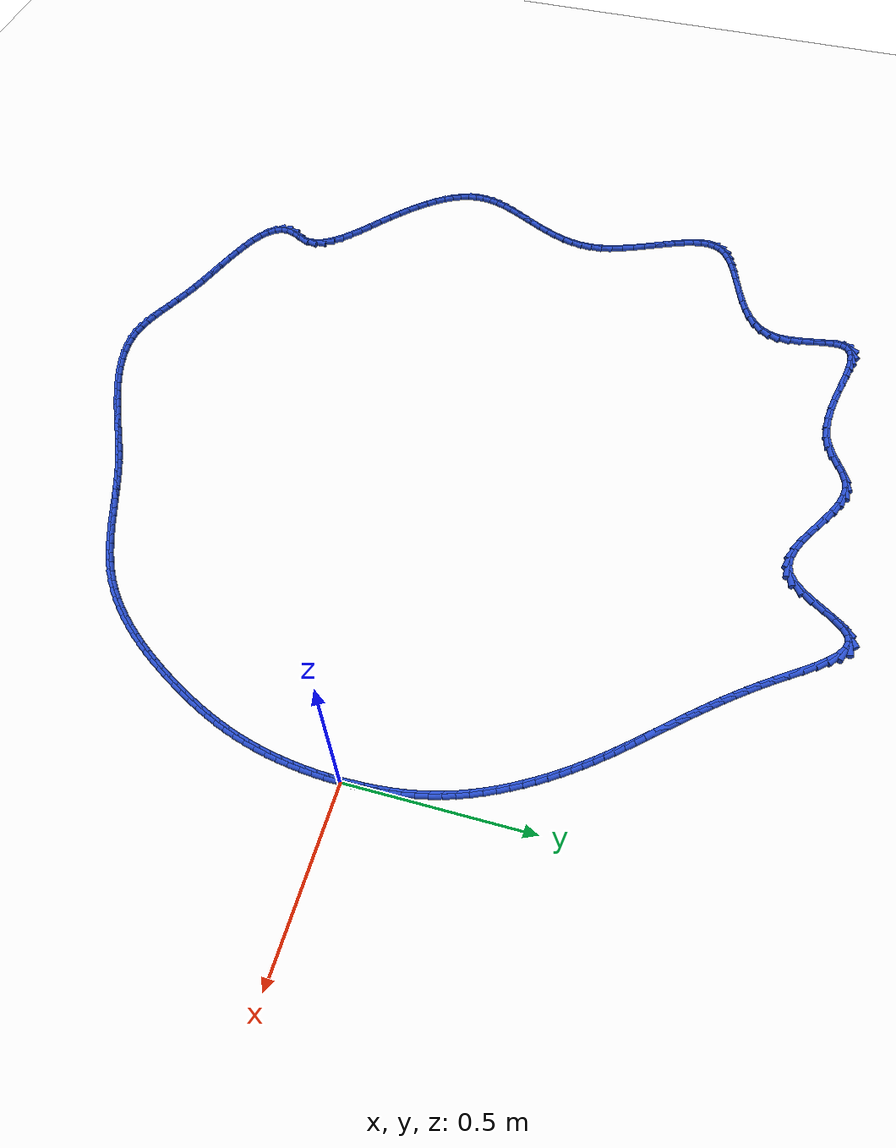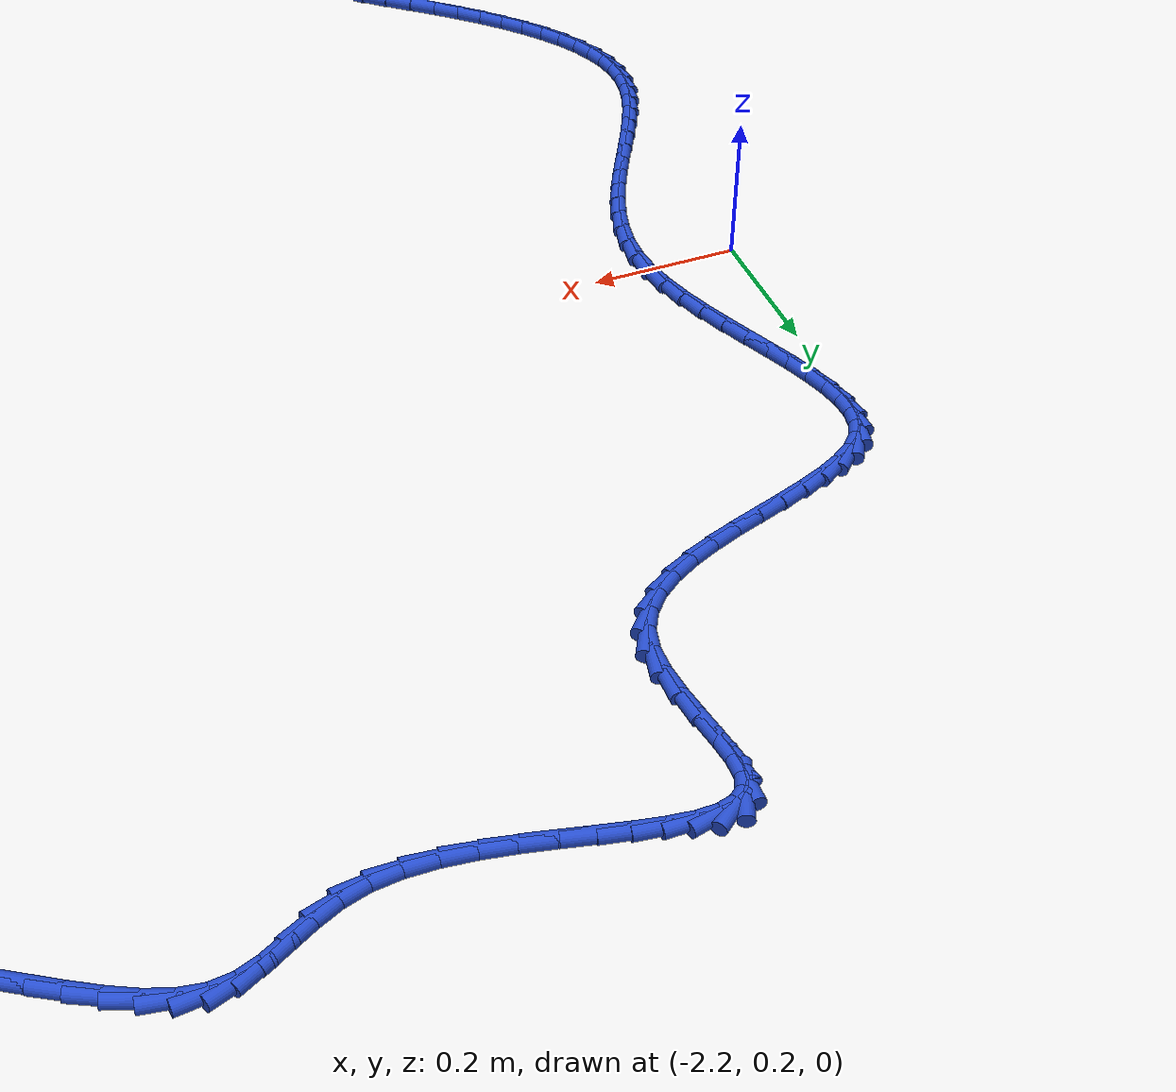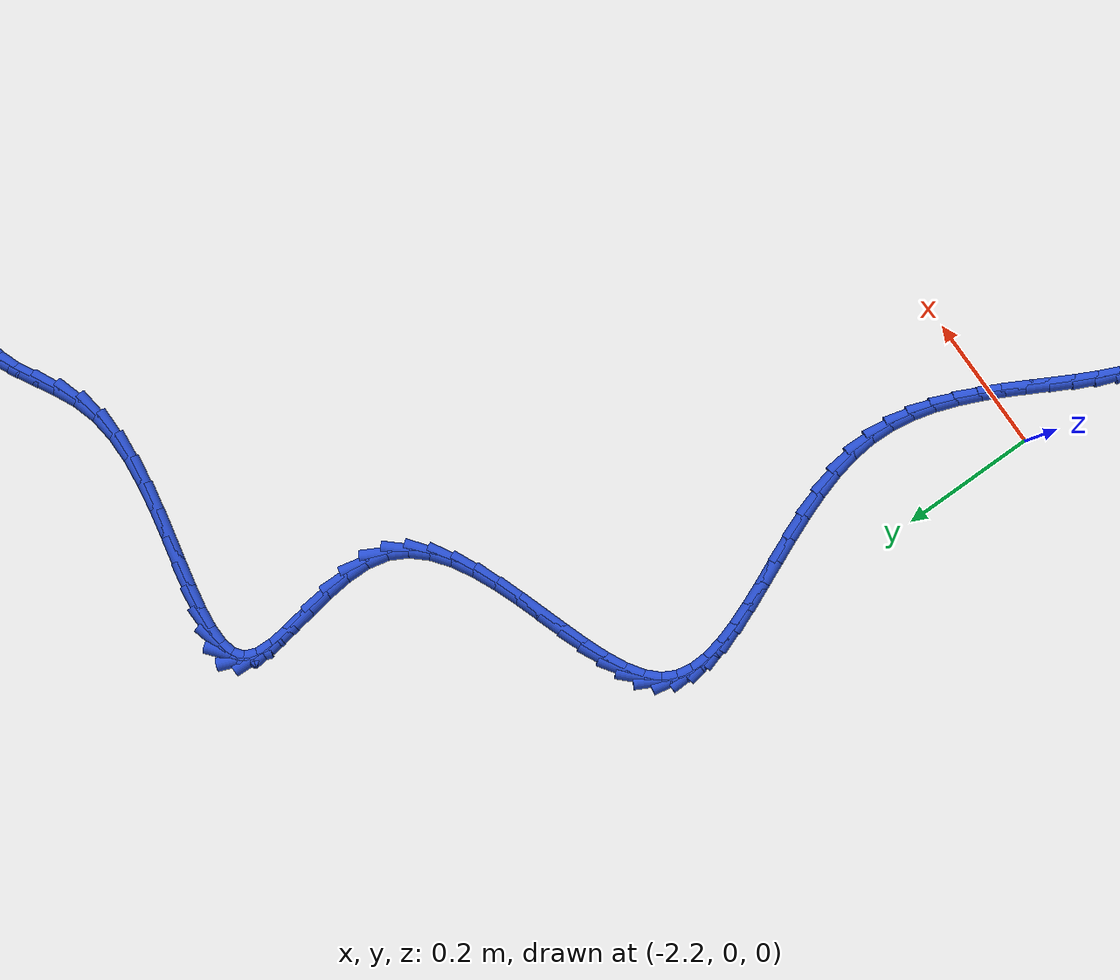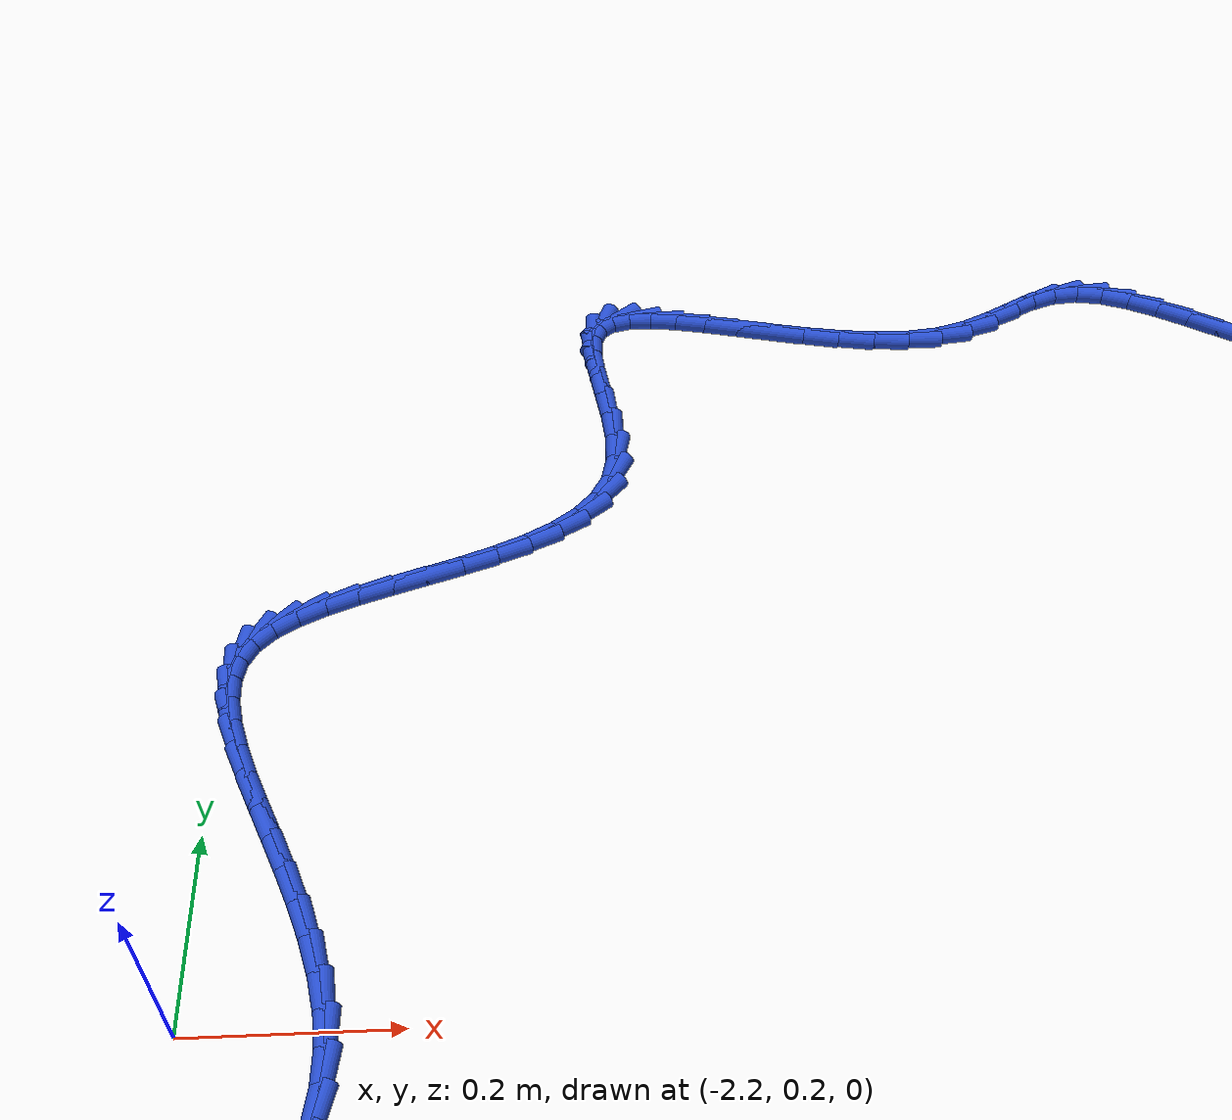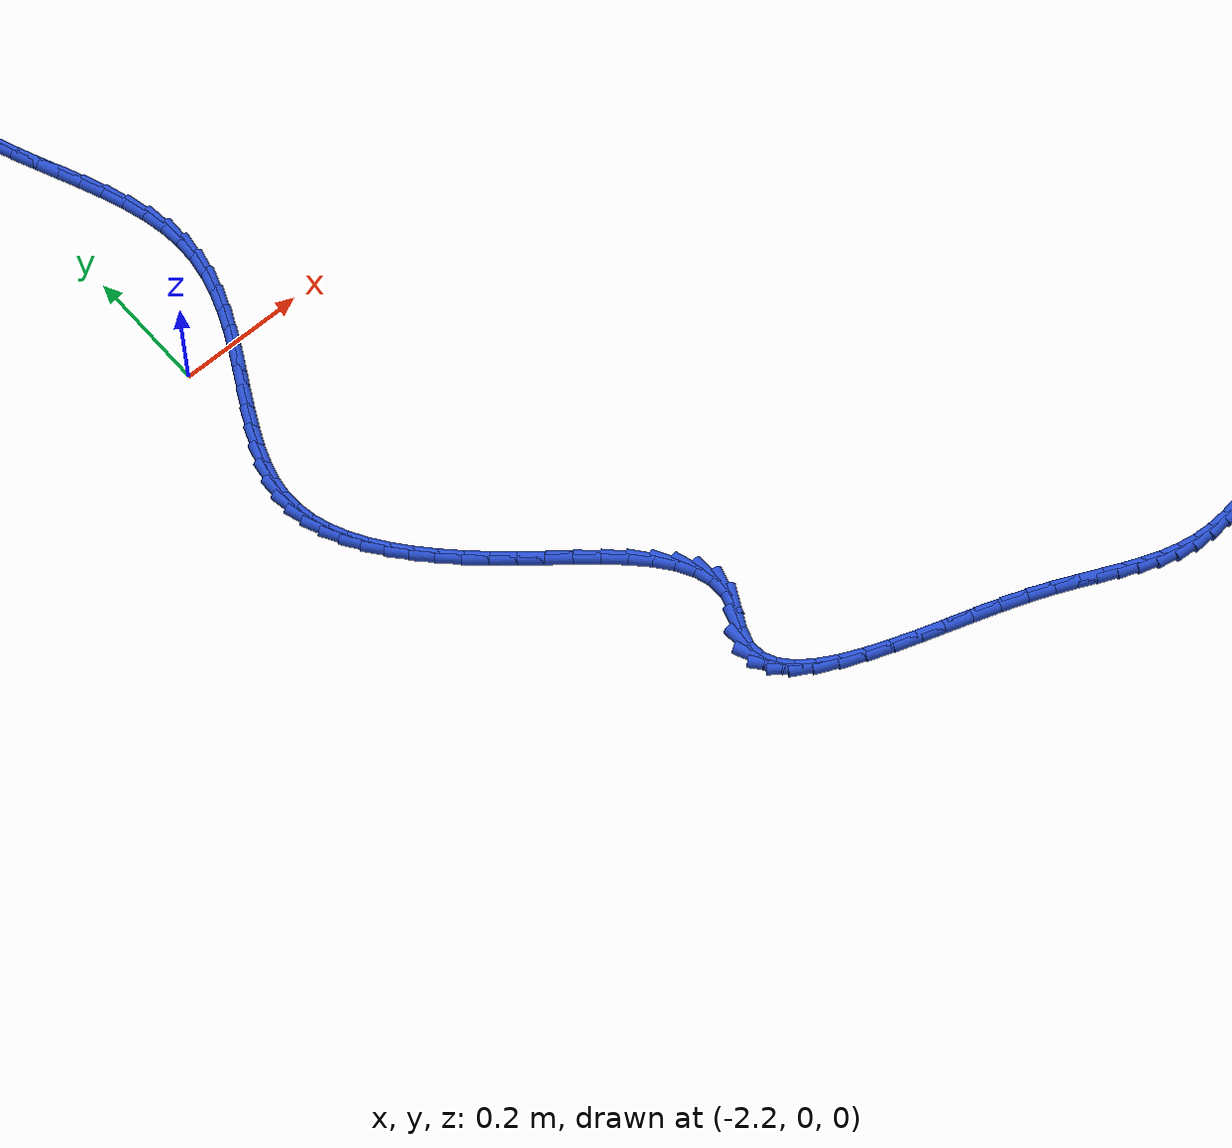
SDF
<sdf version="1.6">
 <world name="default">
  <light name="sun" type="directional">
   <pose>0 0 10 0 -0 0</pose>
   <diffuse>0.8 0.8 0.8 1</diffuse>
   <specular>0.2 0.2 0.2 1</specular>
   <attenuation>
    <range>1000</range>
    <constant>0.9</constant>
    <linear>0.01</linear>
    <quadratic>0.001</quadratic>
   </attenuation>
   <direction>-0.5 0.1 -0.9</direction>
  </light>
  <model name="ground_plane">
   <static>1</static>
   <link name="link">
    <collision name="collision">
     <geometry><plane><normal>0 0 1</normal><size>100 100</size></plane></geometry>
     <surface><friction><ode><mu>100</mu><mu2>50</mu2></ode></friction></surface>
    </collision>
    <visual name="visual">
     <cast_shadows>0</cast_shadows>
     <geometry><plane><normal>0 0 1</normal><size>100 100</size></plane></geometry>
     <material>
      <script><uri>file://media/materials/scripts/gazebo.material</uri><name>Gazebo/WhiteGlow</name></script>
     </material>
    </visual>
   </link>
  </model>
  <gravity>0 0 -9.8</gravity>
  <magnetic_field>6e-06 2.3e-05 -4.2e-05</magnetic_field>
  <atmosphere type="adiabatic"/>
  <physics name="default_physics" default="0" type="ode">
   <max_step_size>0.001</max_step_size>
   <real_time_factor>1</real_time_factor>
   <real_time_update_rate>1000</real_time_update_rate>
  </physics>
  <scene><ambient>0.4 0.4 0.4 1</ambient><background>0.7 0.7 0.7 1</background><shadows>1</shadows></scene>
  <spherical_coordinates>
   <surface_model>EARTH_WGS84</surface_model>
   <latitude_deg>0</latitude_deg>
   <longitude_deg>0</longitude_deg>
   <elevation>0</elevation>
   <heading_deg>0</heading_deg>
  </spherical_coordinates>
  <model name="line">
   <link name="link_0">
    <pose>1.8648277366750676e-17 3.469446951953614e-17 0.01 0 1.57 -1.5646890484324265</pose>
    <collision name="collision">
     <geometry><cylinder><radius>0.01</radius><length>0.08</length></cylinder></geometry>
    </collision>
    <visual name="visual">
     <material>
      <script><name>Gazebo/Blue</name><uri>file://media/materials/scripts/gazebo.material</uri></script>
     </material>
     <geometry><cylinder><radius>0.01</radius><length>0.08</length></cylinder></geometry>
    </visual>
   </link>
   <link name="link_1">
    <pose>-0.00019860160442303806 0.0325184351238313 0.01 0 1.57 -1.5344394550884923</pose>
    <collision name="collision">
     <geometry><cylinder><radius>0.01</radius><length>0.08</length></cylinder></geometry>
    </collision>
    <visual name="visual">
     <material>
      <script><name>Gazebo/Blue</name><uri>file://media/materials/scripts/gazebo.material</uri></script>
     </material>
     <geometry><cylinder><radius>0.01</radius><length>0.08</length></cylinder></geometry>
    </visual>
   </link>
   <link name="link_2">
    <pose>-0.0013794902095978414 0.06498460164728793 0.01 0 1.57 -1.501908289368997</pose>
    <collision name="collision">
     <geometry><cylinder><radius>0.01</radius><length>0.08</length></cylinder></geometry>
    </collision>
    <visual name="visual">
     <material>
      <script><name>Gazebo/Blue</name><uri>file://media/materials/scripts/gazebo.material</uri></script>
     </material>
     <geometry><cylinder><radius>0.01</radius><length>0.08</length></cylinder></geometry>
    </visual>
   </link>
   <link name="link_3">
    <pose>-0.0036135487231357694 0.09736356792599889 0.01 0 1.57 -1.467064574801126</pose>
    <collision name="collision">
     <geometry><cylinder><radius>0.01</radius><length>0.08</length></cylinder></geometry>
    </collision>
    <visual name="visual">
     <material>
      <script><name>Gazebo/Blue</name><uri>file://media/materials/scripts/gazebo.material</uri></script>
     </material>
     <geometry><cylinder><radius>0.01</radius><length>0.08</length></cylinder></geometry>
    </visual>
   </link>
   <link name="link_4">
    <pose>-0.006971660052648199 0.129620402315593 0.01 0 1.57 -1.4298957388029947</pose>
    <collision name="collision">
     <geometry><cylinder><radius>0.01</radius><length>0.08</length></cylinder></geometry>
    </collision>
    <visual name="visual">
     <material>
      <script><name>Gazebo/Blue</name><uri>file://media/materials/scripts/gazebo.material</uri></script>
     </material>
     <geometry><cylinder><radius>0.01</radius><length>0.08</length></cylinder></geometry>
    </visual>
   </link>
   <link name="link_5">
    <pose>-0.011524707105746514 0.1617201731716993 0.01 0 1.57 -1.390413431423118</pose>
    <collision name="collision">
     <geometry><cylinder><radius>0.01</radius><length>0.08</length></cylinder></geometry>
    </collision>
    <visual name="visual">
     <material>
      <script><name>Gazebo/Blue</name><uri>file://media/materials/scripts/gazebo.material</uri></script>
     </material>
     <geometry><cylinder><radius>0.01</radius><length>0.08</length></cylinder></geometry>
    </visual>
   </link>
   <link name="link_6">
    <pose>-0.0173435727900421 0.1936279488499467 0.01 0 1.57 -1.348659549688114</pose>
    <collision name="collision">
     <geometry><cylinder><radius>0.01</radius><length>0.08</length></cylinder></geometry>
    </collision>
    <visual name="visual">
     <material>
      <script><name>Gazebo/Blue</name><uri>file://media/materials/scripts/gazebo.material</uri></script>
     </material>
     <geometry><cylinder><radius>0.01</radius><length>0.08</length></cylinder></geometry>
    </visual>
   </link>
   <link name="link_7">
    <pose>-0.02449914001314632 0.22530879770596393 0.01 0 1.57 -1.3047120747888163</pose>
    <collision name="collision">
     <geometry><cylinder><radius>0.01</radius><length>0.08</length></cylinder></geometry>
    </collision>
    <visual name="visual">
     <material>
      <script><name>Gazebo/Blue</name><uri>file://media/materials/scripts/gazebo.material</uri></script>
     </material>
     <geometry><cylinder><radius>0.01</radius><length>0.08</length></cylinder></geometry>
    </visual>
   </link>
   <link name="link_8">
    <pose>-0.03306229168267055 0.25672778809538 0.01 0 1.57 -1.2588783790772593</pose>
    <collision name="collision">
     <geometry><cylinder><radius>0.01</radius><length>0.08</length></cylinder></geometry>
    </collision>
    <visual name="visual">
     <material>
      <script><name>Gazebo/Blue</name><uri>file://media/materials/scripts/gazebo.material</uri></script>
     </material>
     <geometry><cylinder><radius>0.01</radius><length>0.08</length></cylinder></geometry>
    </visual>
   </link>
   <link name="link_9">
    <pose>-0.043097020539630666 0.28784867324278146 0.01 0 1.57 -1.2142455145818372</pose>
    <collision name="collision">
     <geometry><cylinder><radius>0.01</radius><length>0.08</length></cylinder></geometry>
    </collision>
    <visual name="visual">
     <material>
      <script><name>Gazebo/Blue</name><uri>file://media/materials/scripts/gazebo.material</uri></script>
     </material>
     <geometry><cylinder><radius>0.01</radius><length>0.08</length></cylinder></geometry>
    </visual>
   </link>
   <link name="link_10">
    <pose>-0.05455618170591943 0.31861399345564073 0.01 0 1.57 -1.173005085906663</pose>
    <collision name="collision">
     <geometry><cylinder><radius>0.01</radius><length>0.08</length></cylinder></geometry>
    </collision>
    <visual name="visual">
     <material>
      <script><name>Gazebo/Blue</name><uri>file://media/materials/scripts/gazebo.material</uri></script>
     </material>
     <geometry><cylinder><radius>0.01</radius><length>0.08</length></cylinder></geometry>
    </visual>
   </link>
   <link name="link_11">
    <pose>-0.06730276814858971 0.3489491369874513 0.01 0 1.57 -1.1348899125507856</pose>
    <collision name="collision">
     <geometry><cylinder><radius>0.01</radius><length>0.08</length></cylinder></geometry>
    </collision>
    <visual name="visual">
     <material>
      <script><name>Gazebo/Blue</name><uri>file://media/materials/scripts/gazebo.material</uri></script>
     </material>
     <geometry><cylinder><radius>0.01</radius><length>0.08</length></cylinder></geometry>
    </visual>
   </link>
   <link name="link_12">
    <pose>-0.08119719808007285 0.3787790006464445 0.01 0 1.57 -1.09957542725149</pose>
    <collision name="collision">
     <geometry><cylinder><radius>0.01</radius><length>0.08</length></cylinder></geometry>
    </collision>
    <visual name="visual">
     <material>
      <script><name>Gazebo/Blue</name><uri>file://media/materials/scripts/gazebo.material</uri></script>
     </material>
     <geometry><cylinder><radius>0.01</radius><length>0.08</length></cylinder></geometry>
    </visual>
   </link>
   <link name="link_13">
    <pose>-0.09609988971280017 0.4080284812408514 0.01 0 1.57 -1.0667543839531997</pose>
    <collision name="collision">
     <geometry><cylinder><radius>0.01</radius><length>0.08</length></cylinder></geometry>
    </collision>
    <visual name="visual">
     <material>
      <script><name>Gazebo/Blue</name><uri>file://media/materials/scripts/gazebo.material</uri></script>
     </material>
     <geometry><cylinder><radius>0.01</radius><length>0.08</length></cylinder></geometry>
    </visual>
   </link>
   <link name="link_14">
    <pose>-0.11187126125920314 0.4366224755789035 0.01 0 1.57 -1.0361382040050333</pose>
    <collision name="collision">
     <geometry><cylinder><radius>0.01</radius><length>0.08</length></cylinder></geometry>
    </collision>
    <visual name="visual">
     <material>
      <script><name>Gazebo/Blue</name><uri>file://media/materials/scripts/gazebo.material</uri></script>
     </material>
     <geometry><cylinder><radius>0.01</radius><length>0.08</length></cylinder></geometry>
    </visual>
   </link>
   <link name="link_15">
    <pose>-0.12837173093171306 0.4644858804688318 0.01 0 1.57 -1.0074561668402926</pose>
    <collision name="collision">
     <geometry><cylinder><radius>0.01</radius><length>0.08</length></cylinder></geometry>
    </collision>
    <visual name="visual">
     <material>
      <script><name>Gazebo/Blue</name><uri>file://media/materials/scripts/gazebo.material</uri></script>
     </material>
     <geometry><cylinder><radius>0.01</radius><length>0.08</length></cylinder></geometry>
    </visual>
   </link>
   <link name="link_16">
    <pose>-0.1454617169427613 0.49154359271886755 0.01 0 1.57 -0.9804530227655115</pose>
    <collision name="collision">
     <geometry><cylinder><radius>0.01</radius><length>0.08</length></cylinder></geometry>
    </collision>
    <visual name="visual">
     <material>
      <script><name>Gazebo/Blue</name><uri>file://media/materials/scripts/gazebo.material</uri></script>
     </material>
     <geometry><cylinder><radius>0.01</radius><length>0.08</length></cylinder></geometry>
    </visual>
   </link>
   <link name="link_17">
    <pose>-0.1630016375047793 0.5177205091372424 0.01 0 1.57 -0.9549056445679797</pose>
    <collision name="collision">
     <geometry><cylinder><radius>0.01</radius><length>0.08</length></cylinder></geometry>
    </collision>
    <visual name="visual">
     <material>
      <script><name>Gazebo/Blue</name><uri>file://media/materials/scripts/gazebo.material</uri></script>
     </material>
     <geometry><cylinder><radius>0.01</radius><length>0.08</length></cylinder></geometry>
    </visual>
   </link>
   <link name="link_18">
    <pose>-0.18085951757300536 0.5429533607634174 0.01 0 1.57 -0.9309606497154502</pose>
    <collision name="collision">
     <geometry><cylinder><radius>0.01</radius><length>0.08</length></cylinder></geometry>
    </collision>
    <visual name="visual">
     <material>
      <script><name>Gazebo/Blue</name><uri>file://media/materials/scripts/gazebo.material</uri></script>
     </material>
     <geometry><cylinder><radius>0.01</radius><length>0.08</length></cylinder></geometry>
    </visual>
   </link>
   <link name="link_19">
    <pose>-0.19898627697838736 0.5673078427877206 0.01 0 1.57 -0.9090793045670862</pose>
    <collision name="collision">
     <geometry><cylinder><radius>0.01</radius><length>0.08</length></cylinder></geometry>
    </collision>
    <visual name="visual">
     <material>
      <script><name>Gazebo/Blue</name><uri>file://media/materials/scripts/gazebo.material</uri></script>
     </material>
     <geometry><cylinder><radius>0.01</radius><length>0.08</length></cylinder></geometry>
    </visual>
   </link>
   <link name="link_20">
    <pose>-0.2173838007001097 0.5909289397052757 0.01 0 1.57 -0.8896338132908254</pose>
    <collision name="collision">
     <geometry><cylinder><radius>0.01</radius><length>0.08</length></cylinder></geometry>
    </collision>
    <visual name="visual">
     <material>
      <script><name>Gazebo/Blue</name><uri>file://media/materials/scripts/gazebo.material</uri></script>
     </material>
     <geometry><cylinder><radius>0.01</radius><length>0.08</length></cylinder></geometry>
    </visual>
   </link>
   <link name="link_21">
    <pose>-0.2360547169538202 0.6139627923053499 0.01 0 1.57 -0.872940804313433</pose>
    <collision name="collision">
     <geometry><cylinder><radius>0.01</radius><length>0.08</length></cylinder></geometry>
    </collision>
    <visual name="visual">
     <material>
      <script><name>Gazebo/Blue</name><uri>file://media/materials/scripts/gazebo.material</uri></script>
     </material>
     <geometry><cylinder><radius>0.01</radius><length>0.08</length></cylinder></geometry>
    </visual>
   </link>
   <link name="link_22">
    <pose>-0.25500165395516655 0.6365555413772108 0.01 0 1.57 -0.8592508560091076</pose>
    <collision name="collision">
     <geometry><cylinder><radius>0.01</radius><length>0.08</length></cylinder></geometry>
    </collision>
    <visual name="visual">
     <material>
      <script><name>Gazebo/Blue</name><uri>file://media/materials/scripts/gazebo.material</uri></script>
     </material>
     <geometry><cylinder><radius>0.01</radius><length>0.08</length></cylinder></geometry>
    </visual>
   </link>
   <link name="link_23">
    <pose>-0.27422723991979653 0.6588533277101263 0.01 0 1.57 -0.8487402427142783</pose>
    <collision name="collision">
     <geometry><cylinder><radius>0.01</radius><length>0.08</length></cylinder></geometry>
    </collision>
    <visual name="visual">
     <material>
      <script><name>Gazebo/Blue</name><uri>file://media/materials/scripts/gazebo.material</uri></script>
     </material>
     <geometry><cylinder><radius>0.01</radius><length>0.08</length></cylinder></geometry>
    </visual>
   </link>
   <link name="link_24">
    <pose>-0.2937341030633579 0.6810022920933635 0.01 0 1.57 -0.8415070738261997</pose>
    <collision name="collision">
     <geometry><cylinder><radius>0.01</radius><length>0.08</length></cylinder></geometry>
    </collision>
    <visual name="visual">
     <material>
      <script><name>Gazebo/Blue</name><uri>file://media/materials/scripts/gazebo.material</uri></script>
     </material>
     <geometry><cylinder><radius>0.01</radius><length>0.08</length></cylinder></geometry>
    </visual>
   </link>
   <link name="link_25">
    <pose>-0.31352487160149817 0.7031485753161901 0.01 0 1.57 -0.8375715654040403</pose>
    <collision name="collision">
     <geometry><cylinder><radius>0.01</radius><length>0.08</length></cylinder></geometry>
    </collision>
    <visual name="visual">
     <material>
      <script><name>Gazebo/Blue</name><uri>file://media/materials/scripts/gazebo.material</uri></script>
     </material>
     <geometry><cylinder><radius>0.01</radius><length>0.08</length></cylinder></geometry>
    </visual>
   </link>
   <link name="link_26">
    <pose>-0.33360217374986545 0.7254383181678742 0.01 0 1.57 -0.8368798821241888</pose>
    <collision name="collision">
     <geometry><cylinder><radius>0.01</radius><length>0.08</length></cylinder></geometry>
    </collision>
    <visual name="visual">
     <material>
      <script><name>Gazebo/Blue</name><uri>file://media/materials/scripts/gazebo.material</uri></script>
     </material>
     <geometry><cylinder><radius>0.01</radius><length>0.08</length></cylinder></geometry>
    </visual>
   </link>
   <link name="link_27">
    <pose>-0.35396863772410725 0.7480176614376832 0.01 0 1.57 -0.8393108401909789</pose>
    <collision name="collision">
     <geometry><cylinder><radius>0.01</radius><length>0.08</length></cylinder></geometry>
    </collision>
    <visual name="visual">
     <material>
      <script><name>Gazebo/Blue</name><uri>file://media/materials/scripts/gazebo.material</uri></script>
     </material>
     <geometry><cylinder><radius>0.01</radius><length>0.08</length></cylinder></geometry>
    </visual>
   </link>
   <link name="link_28">
    <pose>-0.37462689173987146 0.7710327459148845 0.01 0 1.57 -0.8446847346907066</pose>
    <collision name="collision">
     <geometry><cylinder><radius>0.01</radius><length>0.08</length></cylinder></geometry>
    </collision>
    <visual name="visual">
     <material>
      <script><name>Gazebo/Blue</name><uri>file://media/materials/scripts/gazebo.material</uri></script>
     </material>
     <geometry><cylinder><radius>0.01</radius><length>0.08</length></cylinder></geometry>
    </visual>
   </link>
   <link name="link_29">
    <pose>-0.3955795640128057 0.794629712388746 0.01 0 1.57 -0.8527735980368186</pose>
    <collision name="collision">
     <geometry><cylinder><radius>0.01</radius><length>0.08</length></cylinder></geometry>
    </collision>
    <visual name="visual">
     <material>
      <script><name>Gazebo/Blue</name><uri>file://media/materials/scripts/gazebo.material</uri></script>
     </material>
     <geometry><cylinder><radius>0.01</radius><length>0.08</length></cylinder></geometry>
    </visual>
   </link>
   <link name="link_30">
    <pose>-0.4168292827585578 0.8189547016485353 0.01 0 1.57 -0.8633122651643738</pose>
    <collision name="collision">
     <geometry><cylinder><radius>0.01</radius><length>0.08</length></cylinder></geometry>
    </collision>
    <visual name="visual">
     <material>
      <script><name>Gazebo/Blue</name><uri>file://media/materials/scripts/gazebo.material</uri></script>
     </material>
     <geometry><cylinder><radius>0.01</radius><length>0.08</length></cylinder></geometry>
    </visual>
   </link>
   <link name="link_31">
    <pose>-0.43837867619277554 0.8441538544835198 0.01 0 1.57 -0.8760096888918707</pose>
    <collision name="collision">
     <geometry><cylinder><radius>0.01</radius><length>0.08</length></cylinder></geometry>
    </collision>
    <visual name="visual">
     <material>
      <script><name>Gazebo/Blue</name><uri>file://media/materials/scripts/gazebo.material</uri></script>
     </material>
     <geometry><cylinder><radius>0.01</radius><length>0.08</length></cylinder></geometry>
    </visual>
   </link>
   <link name="link_32">
    <pose>-0.46023037253110655 0.8703733116829672 0.01 0 1.57 -0.8905600074523075</pose>
    <collision name="collision">
     <geometry><cylinder><radius>0.01</radius><length>0.08</length></cylinder></geometry>
    </collision>
    <visual name="visual">
     <material>
      <script><name>Gazebo/Blue</name><uri>file://media/materials/scripts/gazebo.material</uri></script>
     </material>
     <geometry><cylinder><radius>0.01</radius><length>0.08</length></cylinder></geometry>
    </visual>
   </link>
   <link name="link_33">
    <pose>-0.4823869999891986 0.8977592140361452 0.01 0 1.57 -0.9066529214686809</pose>
    <collision name="collision">
     <geometry><cylinder><radius>0.01</radius><length>0.08</length></cylinder></geometry>
    </collision>
    <visual name="visual">
     <material>
      <script><name>Gazebo/Blue</name><uri>file://media/materials/scripts/gazebo.material</uri></script>
     </material>
     <geometry><cylinder><radius>0.01</radius><length>0.08</length></cylinder></geometry>
    </visual>
   </link>
   <link name="link_34">
    <pose>-0.5048511867826995 0.9264577023323213 0.01 0 1.57 -0.923983000824628</pose>
    <collision name="collision">
     <geometry><cylinder><radius>0.01</radius><length>0.08</length></cylinder></geometry>
    </collision>
    <visual name="visual">
     <material>
      <script><name>Gazebo/Blue</name><uri>file://media/materials/scripts/gazebo.material</uri></script>
     </material>
     <geometry><cylinder><radius>0.01</radius><length>0.08</length></cylinder></geometry>
    </visual>
   </link>
   <link name="link_35">
    <pose>-0.527625561127257 0.9566149173607632 0.01 0 1.57 -0.9422576217575208</pose>
    <collision name="collision">
     <geometry><cylinder><radius>0.01</radius><length>0.08</length></cylinder></geometry>
    </collision>
    <visual name="visual">
     <material>
      <script><name>Gazebo/Blue</name><uri>file://media/materials/scripts/gazebo.material</uri></script>
     </material>
     <geometry><cylinder><radius>0.01</radius><length>0.08</length></cylinder></geometry>
    </visual>
   </link>
   <link name="link_36">
    <pose>-0.5507127512385188 0.9883769999107385 0.01 0 1.57 -0.9607844410860231</pose>
    <collision name="collision">
     <geometry><cylinder><radius>0.01</radius><length>0.08</length></cylinder></geometry>
    </collision>
    <visual name="visual">
     <material>
      <script><name>Gazebo/Blue</name><uri>file://media/materials/scripts/gazebo.material</uri></script>
     </material>
     <geometry><cylinder><radius>0.01</radius><length>0.08</length></cylinder></geometry>
    </visual>
   </link>
   <link name="link_37">
    <pose>-0.5741128465188915 1.0218565698964357 0.01 0 1.57 -0.9676771164594076</pose>
    <collision name="collision">
     <geometry><cylinder><radius>0.01</radius><length>0.08</length></cylinder></geometry>
    </collision>
    <visual name="visual">
     <material>
      <script><name>Gazebo/Blue</name><uri>file://media/materials/scripts/gazebo.material</uri></script>
     </material>
     <geometry><cylinder><radius>0.01</radius><length>0.08</length></cylinder></geometry>
    </visual>
   </link>
   <link name="link_38">
    <pose>-0.5977511115798656 1.0561783082893161 0.01 0 1.57 -0.9499707633925182</pose>
    <collision name="collision">
     <geometry><cylinder><radius>0.01</radius><length>0.08</length></cylinder></geometry>
    </collision>
    <visual name="visual">
     <material>
      <script><name>Gazebo/Blue</name><uri>file://media/materials/scripts/gazebo.material</uri></script>
     </material>
     <geometry><cylinder><radius>0.01</radius><length>0.08</length></cylinder></geometry>
    </visual>
   </link>
   <link name="link_39">
    <pose>-0.6214675288253579 1.089340884040597 0.01 0 1.57 -0.9026625188892047</pose>
    <collision name="collision">
     <geometry><cylinder><radius>0.01</radius><length>0.08</length></cylinder></geometry>
    </collision>
    <visual name="visual">
     <material>
      <script><name>Gazebo/Blue</name><uri>file://media/materials/scripts/gazebo.material</uri></script>
     </material>
     <geometry><cylinder><radius>0.01</radius><length>0.08</length></cylinder></geometry>
    </visual>
   </link>
   <link name="link_40">
    <pose>-0.645097439136437 1.119281682386315 0.01 0 1.57 -0.8119903719864504</pose>
    <collision name="collision">
     <geometry><cylinder><radius>0.01</radius><length>0.08</length></cylinder></geometry>
    </collision>
    <visual name="visual">
     <material>
      <script><name>Gazebo/Blue</name><uri>file://media/materials/scripts/gazebo.material</uri></script>
     </material>
     <geometry><cylinder><radius>0.01</radius><length>0.08</length></cylinder></geometry>
    </visual>
   </link>
   <link name="link_41">
    <pose>-0.6684761833941717 1.1439380885625081 0.01 0 1.57 -0.6459273108763169</pose>
    <collision name="collision">
     <geometry><cylinder><radius>0.01</radius><length>0.08</length></cylinder></geometry>
    </collision>
    <visual name="visual">
     <material>
      <script><name>Gazebo/Blue</name><uri>file://media/materials/scripts/gazebo.material</uri></script>
     </material>
     <geometry><cylinder><radius>0.01</radius><length>0.08</length></cylinder></geometry>
    </visual>
   </link>
   <link name="link_42">
    <pose>-0.6914391024796307 1.1612474878052133 0.01 0 1.57 -0.33929637585532013</pose>
    <collision name="collision">
     <geometry><cylinder><radius>0.01</radius><length>0.08</length></cylinder></geometry>
    </collision>
    <visual name="visual">
     <material>
      <script><name>Gazebo/Blue</name><uri>file://media/materials/scripts/gazebo.material</uri></script>
     </material>
     <geometry><cylinder><radius>0.01</radius><length>0.08</length></cylinder></geometry>
    </visual>
   </link>
   <link name="link_43">
    <pose>-0.7138215372738825 1.169147265350468 0.01 0 1.57 0.1624570294848196</pose>
    <collision name="collision">
     <geometry><cylinder><radius>0.01</radius><length>0.08</length></cylinder></geometry>
    </collision>
    <visual name="visual">
     <material>
      <script><name>Gazebo/Blue</name><uri>file://media/materials/scripts/gazebo.material</uri></script>
     </material>
     <geometry><cylinder><radius>0.01</radius><length>0.08</length></cylinder></geometry>
    </visual>
   </link>
   <link name="link_44">
    <pose>-0.7354615328666831 1.1656004379472886 0.01 0 1.57 0.6259853376983507</pose>
    <collision name="collision">
     <geometry><cylinder><radius>0.01</radius><length>0.08</length></cylinder></geometry>
    </collision>
    <visual name="visual">
     <material>
      <script><name>Gazebo/Blue</name><uri>file://media/materials/scripts/gazebo.material</uri></script>
     </material>
     <geometry><cylinder><radius>0.01</radius><length>0.08</length></cylinder></geometry>
    </visual>
   </link>
   <link name="link_45">
    <pose>-0.7563970010537291 1.1504644345964286 0.01 0 1.57 0.8553214016721044</pose>
    <collision name="collision">
     <geometry><cylinder><radius>0.01</radius><length>0.08</length></cylinder></geometry>
    </collision>
    <visual name="visual">
     <material>
      <script><name>Gazebo/Blue</name><uri>file://media/materials/scripts/gazebo.material</uri></script>
     </material>
     <geometry><cylinder><radius>0.01</radius><length>0.08</length></cylinder></geometry>
    </visual>
   </link>
   <link name="link_46">
    <pose>-0.7769994614839469 1.1267587457408323 0.01 0 1.57 0.9507750261588497</pose>
    <collision name="collision">
     <geometry><cylinder><radius>0.01</radius><length>0.08</length></cylinder></geometry>
    </collision>
    <visual name="visual">
     <material>
      <script><name>Gazebo/Blue</name><uri>file://media/materials/scripts/gazebo.material</uri></script>
     </material>
     <geometry><cylinder><radius>0.01</radius><length>0.08</length></cylinder></geometry>
    </visual>
   </link>
   <link name="link_47">
    <pose>-0.7976721072135649 1.0978030743604092 0.01 0 1.57 0.9704477656848276</pose>
    <collision name="collision">
     <geometry><cylinder><radius>0.01</radius><length>0.08</length></cylinder></geometry>
    </collision>
    <visual name="visual">
     <material>
      <script><name>Gazebo/Blue</name><uri>file://media/materials/scripts/gazebo.material</uri></script>
     </material>
     <geometry><cylinder><radius>0.01</radius><length>0.08</length></cylinder></geometry>
    </visual>
   </link>
   <link name="link_48">
    <pose>-0.8188181312988106 1.0669171234350685 0.01 0 1.57 0.9294641471270434</pose>
    <collision name="collision">
     <geometry><cylinder><radius>0.01</radius><length>0.08</length></cylinder></geometry>
    </collision>
    <visual name="visual">
     <material>
      <script><name>Gazebo/Blue</name><uri>file://media/materials/scripts/gazebo.material</uri></script>
     </material>
     <geometry><cylinder><radius>0.01</radius><length>0.08</length></cylinder></geometry>
    </visual>
   </link>
   <link name="link_49">
    <pose>-0.8408407267959116 1.0374205959447187 0.01 0 1.57 0.8162689620255424</pose>
    <collision name="collision">
     <geometry><cylinder><radius>0.01</radius><length>0.08</length></cylinder></geometry>
    </collision>
    <visual name="visual">
     <material>
      <script><name>Gazebo/Blue</name><uri>file://media/materials/scripts/gazebo.material</uri></script>
     </material>
     <geometry><cylinder><radius>0.01</radius><length>0.08</length></cylinder></geometry>
    </visual>
   </link>
   <link name="link_50">
    <pose>-0.8641430867610961 1.0126331948692684 0.01 0 1.57 0.5910714861182953</pose>
    <collision name="collision">
     <geometry><cylinder><radius>0.01</radius><length>0.08</length></cylinder></geometry>
    </collision>
    <visual name="visual">
     <material>
      <script><name>Gazebo/Blue</name><uri>file://media/materials/scripts/gazebo.material</uri></script>
     </material>
     <geometry><cylinder><radius>0.01</radius><length>0.08</length></cylinder></geometry>
    </visual>
   </link>
   <link name="link_51">
    <pose>-0.8891272246671217 0.9958661250860087 0.01 0 1.57 0.2512812403217004</pose>
    <collision name="collision">
     <geometry><cylinder><radius>0.01</radius><length>0.08</length></cylinder></geometry>
    </collision>
    <visual name="visual">
     <material>
      <script><name>Gazebo/Blue</name><uri>file://media/materials/scripts/gazebo.material</uri></script>
     </material>
     <geometry><cylinder><radius>0.01</radius><length>0.08</length></cylinder></geometry>
    </visual>
   </link>
   <link name="link_52">
    <pose>-0.9159923673978942 0.9889696509914665 0.01 0 1.57 -0.06018092588847776</pose>
    <collision name="collision">
     <geometry><cylinder><radius>0.01</radius><length>0.08</length></cylinder></geometry>
    </collision>
    <visual name="visual">
     <material>
      <script><name>Gazebo/Blue</name><uri>file://media/materials/scripts/gazebo.material</uri></script>
     </material>
     <geometry><cylinder><radius>0.01</radius><length>0.08</length></cylinder></geometry>
    </visual>
   </link>
   <link name="link_53">
    <pose>-0.944506570252369 0.9906877367767344 0.01 0 1.57 -0.28272036968240244</pose>
    <collision name="collision">
     <geometry><cylinder><radius>0.01</radius><length>0.08</length></cylinder></geometry>
    </collision>
    <visual name="visual">
     <material>
      <script><name>Gazebo/Blue</name><uri>file://media/materials/scripts/gazebo.material</uri></script>
     </material>
     <geometry><cylinder><radius>0.01</radius><length>0.08</length></cylinder></geometry>
    </visual>
   </link>
   <link name="link_54">
    <pose>-0.9743827087020915 0.9993668132257942 0.01 0 1.57 -0.42442650674620214</pose>
    <collision name="collision">
     <geometry><cylinder><radius>0.01</radius><length>0.08</length></cylinder></geometry>
    </collision>
    <visual name="visual">
     <material>
      <script><name>Gazebo/Blue</name><uri>file://media/materials/scripts/gazebo.material</uri></script>
     </material>
     <geometry><cylinder><radius>0.01</radius><length>0.08</length></cylinder></geometry>
    </visual>
   </link>
   <link name="link_55">
    <pose>-1.0053336582186085 1.0133533111226285 0.01 0 1.57 -0.5072856676408173</pose>
    <collision name="collision">
     <geometry><cylinder><radius>0.01</radius><length>0.08</length></cylinder></geometry>
    </collision>
    <visual name="visual">
     <material>
      <script><name>Gazebo/Blue</name><uri>file://media/materials/scripts/gazebo.material</uri></script>
     </material>
     <geometry><cylinder><radius>0.01</radius><length>0.08</length></cylinder></geometry>
    </visual>
   </link>
   <link name="link_56">
    <pose>-1.0370722942734665 1.0309936612512192 0.01 0 1.57 -0.5471683791298421</pose>
    <collision name="collision">
     <geometry><cylinder><radius>0.01</radius><length>0.08</length></cylinder></geometry>
    </collision>
    <visual name="visual">
     <material>
      <script><name>Gazebo/Blue</name><uri>file://media/materials/scripts/gazebo.material</uri></script>
     </material>
     <geometry><cylinder><radius>0.01</radius><length>0.08</length></cylinder></geometry>
    </visual>
   </link>
   <link name="link_57">
    <pose>-1.0693114923382117 1.0506342943955493 0.01 0 1.57 -0.5520235492959567</pose>
    <collision name="collision">
     <geometry><cylinder><radius>0.01</radius><length>0.08</length></cylinder></geometry>
    </collision>
    <visual name="visual">
     <material>
      <script><name>Gazebo/Blue</name><uri>file://media/materials/scripts/gazebo.material</uri></script>
     </material>
     <geometry><cylinder><radius>0.01</radius><length>0.08</length></cylinder></geometry>
    </visual>
   </link>
   <link name="link_58">
    <pose>-1.1017641278843893 1.0706216413395995 0.01 0 1.57 -0.5232859440363107</pose>
    <collision name="collision">
     <geometry><cylinder><radius>0.01</radius><length>0.08</length></cylinder></geometry>
    </collision>
    <visual name="visual">
     <material>
      <script><name>Gazebo/Blue</name><uri>file://media/materials/scripts/gazebo.material</uri></script>
     </material>
     <geometry><cylinder><radius>0.01</radius><length>0.08</length></cylinder></geometry>
    </visual>
   </link>
   <link name="link_59">
    <pose>-1.1341430763835476 1.0893021328673538 0.01 0 1.57 -0.4564006238870125</pose>
    <collision name="collision">
     <geometry><cylinder><radius>0.01</radius><length>0.08</length></cylinder></geometry>
    </collision>
    <visual name="visual">
     <material>
      <script><name>Gazebo/Blue</name><uri>file://media/materials/scripts/gazebo.material</uri></script>
     </material>
     <geometry><cylinder><radius>0.01</radius><length>0.08</length></cylinder></geometry>
    </visual>
   </link>
   <link name="link_60">
    <pose>-1.1661612133072312 1.1050221997627931 0.01 0 1.57 -0.3402627890461633</pose>
    <collision name="collision">
     <geometry><cylinder><radius>0.01</radius><length>0.08</length></cylinder></geometry>
    </collision>
    <visual name="visual">
     <material>
      <script><name>Gazebo/Blue</name><uri>file://media/materials/scripts/gazebo.material</uri></script>
     </material>
     <geometry><cylinder><radius>0.01</radius><length>0.08</length></cylinder></geometry>
    </visual>
   </link>
   <link name="link_61">
    <pose>-1.197531414126988 1.1161282728099007 0.01 0 1.57 -0.15765836590429164</pose>
    <collision name="collision">
     <geometry><cylinder><radius>0.01</radius><length>0.08</length></cylinder></geometry>
    </collision>
    <visual name="visual">
     <material>
      <script><name>Gazebo/Blue</name><uri>file://media/materials/scripts/gazebo.material</uri></script>
     </material>
     <geometry><cylinder><radius>0.01</radius><length>0.08</length></cylinder></geometry>
    </visual>
   </link>
   <link name="link_62">
    <pose>-1.2279665543143623 1.1209667827926577 0.01 0 1.57 0.10263413177115663</pose>
    <collision name="collision">
     <geometry><cylinder><radius>0.01</radius><length>0.08</length></cylinder></geometry>
    </collision>
    <visual name="visual">
     <material>
      <script><name>Gazebo/Blue</name><uri>file://media/materials/scripts/gazebo.material</uri></script>
     </material>
     <geometry><cylinder><radius>0.01</radius><length>0.08</length></cylinder></geometry>
    </visual>
   </link>
   <link name="link_63">
    <pose>-1.2571983899645414 1.117956019732429 0.01 0 1.57 0.35035542812867</pose>
    <collision name="collision">
     <geometry><cylinder><radius>0.01</radius><length>0.08</length></cylinder></geometry>
    </collision>
    <visual name="visual">
     <material>
      <script><name>Gazebo/Blue</name><uri>file://media/materials/scripts/gazebo.material</uri></script>
     </material>
     <geometry><cylinder><radius>0.01</radius><length>0.08</length></cylinder></geometry>
    </visual>
   </link>
   <link name="link_64">
    <pose>-1.285509394476977 1.1076102915710802 0.01 0 1.57 0.48161283132658783</pose>
    <collision name="collision">
     <geometry><cylinder><radius>0.01</radius><length>0.08</length></cylinder></geometry>
    </collision>
    <visual name="visual">
     <material>
      <script><name>Gazebo/Blue</name><uri>file://media/materials/scripts/gazebo.material</uri></script>
     </material>
     <geometry><cylinder><radius>0.01</radius><length>0.08</length></cylinder></geometry>
    </visual>
   </link>
   <link name="link_65">
    <pose>-1.3138064704727535 1.092820470103618 0.01 0 1.57 0.506559227448487</pose>
    <collision name="collision">
     <geometry><cylinder><radius>0.01</radius><length>0.08</length></cylinder></geometry>
    </collision>
    <visual name="visual">
     <material>
      <script><name>Gazebo/Blue</name><uri>file://media/materials/scripts/gazebo.material</uri></script>
     </material>
     <geometry><cylinder><radius>0.01</radius><length>0.08</length></cylinder></geometry>
    </visual>
   </link>
   <link name="link_66">
    <pose>-1.3430302165420716 1.0766056732407399 0.01 0 1.57 0.43956839144852444</pose>
    <collision name="collision">
     <geometry><cylinder><radius>0.01</radius><length>0.08</length></cylinder></geometry>
    </collision>
    <visual name="visual">
     <material>
      <script><name>Gazebo/Blue</name><uri>file://media/materials/scripts/gazebo.material</uri></script>
     </material>
     <geometry><cylinder><radius>0.01</radius><length>0.08</length></cylinder></geometry>
    </visual>
   </link>
   <link name="link_67">
    <pose>-1.3741212312751294 1.061985018893143 0.01 0 1.57 0.28851569758027024</pose>
    <collision name="collision">
     <geometry><cylinder><radius>0.01</radius><length>0.08</length></cylinder></geometry>
    </collision>
    <visual name="visual">
     <material>
      <script><name>Gazebo/Blue</name><uri>file://media/materials/scripts/gazebo.material</uri></script>
     </material>
     <geometry><cylinder><radius>0.01</radius><length>0.08</length></cylinder></geometry>
    </visual>
   </link>
   <link name="link_68">
    <pose>-1.4079995198568007 1.0519300437578145 0.01 0 1.57 0.1149981122758367</pose>
    <collision name="collision">
     <geometry><cylinder><radius>0.01</radius><length>0.08</length></cylinder></geometry>
    </collision>
    <visual name="visual">
     <material>
      <script><name>Gazebo/Blue</name><uri>file://media/materials/scripts/gazebo.material</uri></script>
     </material>
     <geometry><cylinder><radius>0.01</radius><length>0.08</length></cylinder></geometry>
    </visual>
   </link>
   <link name="link_69">
    <pose>-1.4448333753994742 1.047675448287256 0.01 0 1.57 -0.015059358832556541</pose>
    <collision name="collision">
     <geometry><cylinder><radius>0.01</radius><length>0.08</length></cylinder></geometry>
    </collision>
    <visual name="visual">
     <material>
      <script><name>Gazebo/Blue</name><uri>file://media/materials/scripts/gazebo.material</uri></script>
     </material>
     <geometry><cylinder><radius>0.01</radius><length>0.08</length></cylinder></geometry>
    </visual>
   </link>
   <link name="link_70">
    <pose>-1.4838419505008476 1.0482629368289826 0.01 0 1.57 -0.1069459673614197</pose>
    <collision name="collision">
     <geometry><cylinder><radius>0.01</radius><length>0.08</length></cylinder></geometry>
    </collision>
    <visual name="visual">
     <material>
      <script><name>Gazebo/Blue</name><uri>file://media/materials/scripts/gazebo.material</uri></script>
     </material>
     <geometry><cylinder><radius>0.01</radius><length>0.08</length></cylinder></geometry>
    </visual>
   </link>
   <link name="link_71">
    <pose>-1.5241836442872767 1.0525938423903864 0.01 0 1.57 -0.16919954219452152</pose>
    <collision name="collision">
     <geometry><cylinder><radius>0.01</radius><length>0.08</length></cylinder></geometry>
    </collision>
    <visual name="visual">
     <material>
      <script><name>Gazebo/Blue</name><uri>file://media/materials/scripts/gazebo.material</uri></script>
     </material>
     <geometry><cylinder><radius>0.01</radius><length>0.08</length></cylinder></geometry>
    </visual>
   </link>
   <link name="link_72">
    <pose>-1.5650168558851192 1.0595694979788597 0.01 0 1.57 -0.20747197507004378</pose>
    <collision name="collision">
     <geometry><cylinder><radius>0.01</radius><length>0.08</length></cylinder></geometry>
    </collision>
    <visual name="visual">
     <material>
      <script><name>Gazebo/Blue</name><uri>file://media/materials/scripts/gazebo.material</uri></script>
     </material>
     <geometry><cylinder><radius>0.01</radius><length>0.08</length></cylinder></geometry>
    </visual>
   </link>
   <link name="link_73">
    <pose>-1.6054999844207316 1.0680912366017934 0.01 0 1.57 -0.22442702422163446</pose>
    <collision name="collision">
     <geometry><cylinder><radius>0.01</radius><length>0.08</length></cylinder></geometry>
    </collision>
    <visual name="visual">
     <material>
      <script><name>Gazebo/Blue</name><uri>file://media/materials/scripts/gazebo.material</uri></script>
     </material>
     <geometry><cylinder><radius>0.01</radius><length>0.08</length></cylinder></geometry>
    </visual>
   </link>
   <link name="link_74">
    <pose>-1.6447914290204715 1.0770603912665795 0.01 0 1.57 -0.21964864377895948</pose>
    <collision name="collision">
     <geometry><cylinder><radius>0.01</radius><length>0.08</length></cylinder></geometry>
    </collision>
    <visual name="visual">
     <material>
      <script><name>Gazebo/Blue</name><uri>file://media/materials/scripts/gazebo.material</uri></script>
     </material>
     <geometry><cylinder><radius>0.01</radius><length>0.08</length></cylinder></geometry>
    </visual>
   </link>
   <link name="link_75">
    <pose>-1.6820495888106946 1.0853782949806097 0.01 0 1.57 -0.188748825636155</pose>
    <collision name="collision">
     <geometry><cylinder><radius>0.01</radius><length>0.08</length></cylinder></geometry>
    </collision>
    <visual name="visual">
     <material>
      <script><name>Gazebo/Blue</name><uri>file://media/materials/scripts/gazebo.material</uri></script>
     </material>
     <geometry><cylinder><radius>0.01</radius><length>0.08</length></cylinder></geometry>
    </visual>
   </link>
   <link name="link_76">
    <pose>-1.7164328629177577 1.0919462807512754 0.01 0 1.57 -0.1206948329132145</pose>
    <collision name="collision">
     <geometry><cylinder><radius>0.01</radius><length>0.08</length></cylinder></geometry>
    </collision>
    <visual name="visual">
     <material>
      <script><name>Gazebo/Blue</name><uri>file://media/materials/scripts/gazebo.material</uri></script>
     </material>
     <geometry><cylinder><radius>0.01</radius><length>0.08</length></cylinder></geometry>
    </visual>
   </link>
   <link name="link_77">
    <pose>-1.7470996504680192 1.0956656815859689 0.01 0 1.57 0.00872679638063249</pose>
    <collision name="collision">
     <geometry><cylinder><radius>0.01</radius><length>0.08</length></cylinder></geometry>
    </collision>
    <visual name="visual">
     <material>
      <script><name>Gazebo/Blue</name><uri>file://media/materials/scripts/gazebo.material</uri></script>
     </material>
     <geometry><cylinder><radius>0.01</radius><length>0.08</length></cylinder></geometry>
    </visual>
   </link>
   <link name="link_78">
    <pose>-1.7732083505878338 1.0954378304920809 0.01 0 1.57 0.24936030623793817</pose>
    <collision name="collision">
     <geometry><cylinder><radius>0.01</radius><length>0.08</length></cylinder></geometry>
    </collision>
    <visual name="visual">
     <material>
      <script><name>Gazebo/Blue</name><uri>file://media/materials/scripts/gazebo.material</uri></script>
     </material>
     <geometry><cylinder><radius>0.01</radius><length>0.08</length></cylinder></geometry>
    </visual>
   </link>
   <link name="link_79">
    <pose>-1.7939173624035605 1.0901640604770044 0.01 0 1.57 0.6681390767789892</pose>
    <collision name="collision">
     <geometry><cylinder><radius>0.01</radius><length>0.08</length></cylinder></geometry>
    </collision>
    <visual name="visual">
     <material>
      <script><name>Gazebo/Blue</name><uri>file://media/materials/scripts/gazebo.material</uri></script>
     </material>
     <geometry><cylinder><radius>0.01</radius><length>0.08</length></cylinder></geometry>
    </visual>
   </link>
   <link name="link_80">
    <pose>-1.808385085041555 1.0787457045481303 0.01 0 1.57 1.1915108120711917</pose>
    <collision name="collision">
     <geometry><cylinder><radius>0.01</radius><length>0.08</length></cylinder></geometry>
    </collision>
    <visual name="visual">
     <material>
      <script><name>Gazebo/Blue</name><uri>file://media/materials/scripts/gazebo.material</uri></script>
     </material>
     <geometry><cylinder><radius>0.01</radius><length>0.08</length></cylinder></geometry>
    </visual>
   </link>
   <link name="link_81">
    <pose>-1.815808707168012 1.0601207396804573 0.01 0 1.57 1.5363126488230165</pose>
    <collision name="collision">
     <geometry><cylinder><radius>0.01</radius><length>0.08</length></cylinder></geometry>
    </collision>
    <visual name="visual">
     <material>
      <script><name>Gazebo/Blue</name><uri>file://media/materials/scripts/gazebo.material</uri></script>
     </material>
     <geometry><cylinder><radius>0.01</radius><length>0.08</length></cylinder></geometry>
    </visual>
   </link>
   <link name="link_82">
    <pose>-1.8166938251167422 1.034463178346942 0.01 0 1.57 -1.4566506864139475</pose>
    <collision name="collision">
     <geometry><cylinder><radius>0.01</radius><length>0.08</length></cylinder></geometry>
    </collision>
    <visual name="visual">
     <material>
      <script><name>Gazebo/Blue</name><uri>file://media/materials/scripts/gazebo.material</uri></script>
     </material>
     <geometry><cylinder><radius>0.01</radius><length>0.08</length></cylinder></geometry>
    </visual>
   </link>
   <link name="link_83">
    <pose>-1.8131385145156196 1.0034514272441006 0.01 0 1.57 -1.4046557177342809</pose>
    <collision name="collision">
     <geometry><cylinder><radius>0.01</radius><length>0.08</length></cylinder></geometry>
    </collision>
    <visual name="visual">
     <material>
      <script><name>Gazebo/Blue</name><uri>file://media/materials/scripts/gazebo.material</uri></script>
     </material>
     <geometry><cylinder><radius>0.01</radius><length>0.08</length></cylinder></geometry>
    </visual>
   </link>
   <link name="link_84">
    <pose>-1.8073371432951784 0.9688548591390522 0.01 0 1.57 -1.411414343905852</pose>
    <collision name="collision">
     <geometry><cylinder><radius>0.01</radius><length>0.08</length></cylinder></geometry>
    </collision>
    <visual name="visual">
     <material>
      <script><name>Gazebo/Blue</name><uri>file://media/materials/scripts/gazebo.material</uri></script>
     </material>
     <geometry><cylinder><radius>0.01</radius><length>0.08</length></cylinder></geometry>
    </visual>
   </link>
   <link name="link_85">
    <pose>-1.801484079385951 0.9324428467989141 0.01 0 1.57 -1.4693741646954077</pose>
    <collision name="collision">
     <geometry><cylinder><radius>0.01</radius><length>0.08</length></cylinder></geometry>
    </collision>
    <visual name="visual">
     <material>
      <script><name>Gazebo/Blue</name><uri>file://media/materials/scripts/gazebo.material</uri></script>
     </material>
     <geometry><cylinder><radius>0.01</radius><length>0.08</length></cylinder></geometry>
    </visual>
   </link>
   <link name="link_86">
    <pose>-1.7977736907184731 0.8959847629908058 0.01 0 1.57 1.552757160157416</pose>
    <collision name="collision">
     <geometry><cylinder><radius>0.01</radius><length>0.08</length></cylinder></geometry>
    </collision>
    <visual name="visual">
     <material>
      <script><name>Gazebo/Blue</name><uri>file://media/materials/scripts/gazebo.material</uri></script>
     </material>
     <geometry><cylinder><radius>0.01</radius><length>0.08</length></cylinder></geometry>
    </visual>
   </link>
   <link name="link_87">
    <pose>-1.798400345223278 0.8612499804818452 0.01 0 1.57 1.3465627687297979</pose>
    <collision name="collision">
     <geometry><cylinder><radius>0.01</radius><length>0.08</length></cylinder></geometry>
    </collision>
    <visual name="visual">
     <material>
      <script><name>Gazebo/Blue</name><uri>file://media/materials/scripts/gazebo.material</uri></script>
     </material>
     <geometry><cylinder><radius>0.01</radius><length>0.08</length></cylinder></geometry>
    </visual>
   </link>
   <link name="link_88">
    <pose>-1.8055302290130575 0.8299880102878057 0.01 0 1.57 1.077619597262096</pose>
    <collision name="collision">
     <geometry><cylinder><radius>0.01</radius><length>0.08</length></cylinder></geometry>
    </collision>
    <visual name="visual">
     <material>
      <script><name>Gazebo/Blue</name><uri>file://media/materials/scripts/gazebo.material</uri></script>
     </material>
     <geometry><cylinder><radius>0.01</radius><length>0.08</length></cylinder></geometry>
    </visual>
   </link>
   <link name="link_89">
    <pose>-1.8200214144070368 0.8030264416718508 0.01 0 1.57 0.8364624396245434</pose>
    <collision name="collision">
     <geometry><cylinder><radius>0.01</radius><length>0.08</length></cylinder></geometry>
    </collision>
    <visual name="visual">
     <material>
      <script><name>Gazebo/Blue</name><uri>file://media/materials/scripts/gazebo.material</uri></script>
     </material>
     <geometry><cylinder><radius>0.01</radius><length>0.08</length></cylinder></geometry>
    </visual>
   </link>
   <link name="link_90">
    <pose>-1.8408983513571147 0.7799005785050358 0.01 0 1.57 0.6493220028345495</pose>
    <collision name="collision">
     <geometry><cylinder><radius>0.01</radius><length>0.08</length></cylinder></geometry>
    </collision>
    <visual name="visual">
     <material>
      <script><name>Gazebo/Blue</name><uri>file://media/materials/scripts/gazebo.material</uri></script>
     </material>
     <geometry><cylinder><radius>0.01</radius><length>0.08</length></cylinder></geometry>
    </visual>
   </link>
   <link name="link_91">
    <pose>-1.8670484343479166 0.7600491318258795 0.01 0 1.57 0.5146070128000414</pose>
    <collision name="collision">
     <geometry><cylinder><radius>0.01</radius><length>0.08</length></cylinder></geometry>
    </collision>
    <visual name="visual">
     <material>
      <script><name>Gazebo/Blue</name><uri>file://media/materials/scripts/gazebo.material</uri></script>
     </material>
     <geometry><cylinder><radius>0.01</radius><length>0.08</length></cylinder></geometry>
    </visual>
   </link>
   <link name="link_92">
    <pose>-1.8973590578640687 0.7429108126728989 0.01 0 1.57 0.4222337463207874</pose>
    <collision name="collision">
     <geometry><cylinder><radius>0.01</radius><length>0.08</length></cylinder></geometry>
    </collision>
    <visual name="visual">
     <material>
      <script><name>Gazebo/Blue</name><uri>file://media/materials/scripts/gazebo.material</uri></script>
     </material>
     <geometry><cylinder><radius>0.01</radius><length>0.08</length></cylinder></geometry>
    </visual>
   </link>
   <link name="link_93">
    <pose>-1.9307176163901962 0.7279243320846128 0.01 0 1.57 0.36275709491214153</pose>
    <collision name="collision">
     <geometry><cylinder><radius>0.01</radius><length>0.08</length></cylinder></geometry>
    </collision>
    <visual name="visual">
     <material>
      <script><name>Gazebo/Blue</name><uri>file://media/materials/scripts/gazebo.material</uri></script>
     </material>
     <geometry><cylinder><radius>0.01</radius><length>0.08</length></cylinder></geometry>
    </visual>
   </link>
   <link name="link_94">
    <pose>-1.966011504410926 0.714528401099539 0.01 0 1.57 0.3298967251809626</pose>
    <collision name="collision">
     <geometry><cylinder><radius>0.01</radius><length>0.08</length></cylinder></geometry>
    </collision>
    <visual name="visual">
     <material>
      <script><name>Gazebo/Blue</name><uri>file://media/materials/scripts/gazebo.material</uri></script>
     </material>
     <geometry><cylinder><radius>0.01</radius><length>0.08</length></cylinder></geometry>
    </visual>
   </link>
   <link name="link_95">
    <pose>-2.0021281164108835 0.7021617307561954 0.01 0 1.57 0.32065627028727683</pose>
    <collision name="collision">
     <geometry><cylinder><radius>0.01</radius><length>0.08</length></cylinder></geometry>
    </collision>
    <visual name="visual">
     <material>
      <script><name>Gazebo/Blue</name><uri>file://media/materials/scripts/gazebo.material</uri></script>
     </material>
     <geometry><cylinder><radius>0.01</radius><length>0.08</length></cylinder></geometry>
    </visual>
   </link>
   <link name="link_96">
    <pose>-2.037954846874694 0.6902630320930997 0.01 0 1.57 0.33521269895352146</pose>
    <collision name="collision">
     <geometry><cylinder><radius>0.01</radius><length>0.08</length></cylinder></geometry>
    </collision>
    <visual name="visual">
     <material>
      <script><name>Gazebo/Blue</name><uri>file://media/materials/scripts/gazebo.material</uri></script>
     </material>
     <geometry><cylinder><radius>0.01</radius><length>0.08</length></cylinder></geometry>
    </visual>
   </link>
   <link name="link_97">
    <pose>-2.0723790902869843 0.6782710161487704 0.01 0 1.57 0.37734043916184085</pose>
    <collision name="collision">
     <geometry><cylinder><radius>0.01</radius><length>0.08</length></cylinder></geometry>
    </collision>
    <visual name="visual">
     <material>
      <script><name>Gazebo/Blue</name><uri>file://media/materials/scripts/gazebo.material</uri></script>
     </material>
     <geometry><cylinder><radius>0.01</radius><length>0.08</length></cylinder></geometry>
    </visual>
   </link>
   <link name="link_98">
    <pose>-2.104288241132379 0.6656243939617252 0.01 0 1.57 0.4557469620426859</pose>
    <collision name="collision">
     <geometry><cylinder><radius>0.01</radius><length>0.08</length></cylinder></geometry>
    </collision>
    <visual name="visual">
     <material>
      <script><name>Gazebo/Blue</name><uri>file://media/materials/scripts/gazebo.material</uri></script>
     </material>
     <geometry><cylinder><radius>0.01</radius><length>0.08</length></cylinder></geometry>
    </visual>
   </link>
   <link name="link_99">
    <pose>-2.1325696938955057 0.651761876570482 0.01 0 1.57 0.586401141765999</pose>
    <collision name="collision">
     <geometry><cylinder><radius>0.01</radius><length>0.08</length></cylinder></geometry>
    </collision>
    <visual name="visual">
     <material>
      <script><name>Gazebo/Blue</name><uri>file://media/materials/scripts/gazebo.material</uri></script>
     </material>
     <geometry><cylinder><radius>0.01</radius><length>0.08</length></cylinder></geometry>
    </visual>
   </link>
   <link name="link_100">
    <pose>-2.156110843060989 0.6361221750135593 0.01 0 1.57 0.7935270501261672</pose>
    <collision name="collision">
     <geometry><cylinder><radius>0.01</radius><length>0.08</length></cylinder></geometry>
    </collision>
    <visual name="visual">
     <material>
      <script><name>Gazebo/Blue</name><uri>file://media/materials/scripts/gazebo.material</uri></script>
     </material>
     <geometry><cylinder><radius>0.01</radius><length>0.08</length></cylinder></geometry>
    </visual>
   </link>
   <link name="link_101">
    <pose>-2.1737990831134555 0.6181440003294743 0.01 0 1.57 1.0851061813735285</pose>
    <collision name="collision">
     <geometry><cylinder><radius>0.01</radius><length>0.08</length></cylinder></geometry>
    </collision>
    <visual name="visual">
     <material>
      <script><name>Gazebo/Blue</name><uri>file://media/materials/scripts/gazebo.material</uri></script>
     </material>
     <geometry><cylinder><radius>0.01</radius><length>0.08</length></cylinder></geometry>
    </visual>
   </link>
   <link name="link_102">
    <pose>-2.1847656421468593 0.5973686819829471 0.01 0 1.57 1.3742562967150136</pose>
    <collision name="collision">
     <geometry><cylinder><radius>0.01</radius><length>0.08</length></cylinder></geometry>
    </collision>
    <visual name="visual">
     <material>
      <script><name>Gazebo/Blue</name><uri>file://media/materials/scripts/gazebo.material</uri></script>
     </material>
     <geometry><cylinder><radius>0.01</radius><length>0.08</length></cylinder></geometry>
    </visual>
   </link>
   <link name="link_103">
    <pose>-2.18944157010138 0.5738845850691354 0.01 0 1.57 -1.5417851789253603</pose>
    <collision name="collision">
     <geometry><cylinder><radius>0.01</radius><length>0.08</length></cylinder></geometry>
    </collision>
    <visual name="visual">
     <material>
      <script><name>Gazebo/Blue</name><uri>file://media/materials/scripts/gazebo.material</uri></script>
     </material>
     <geometry><cylinder><radius>0.01</radius><length>0.08</length></cylinder></geometry>
    </visual>
   </link>
   <link name="link_104">
    <pose>-2.188689304240473 0.5479616258988812 0.01 0 1.57 -1.3837113470608586</pose>
    <collision name="collision">
     <geometry><cylinder><radius>0.01</radius><length>0.08</length></cylinder></geometry>
    </collision>
    <visual name="visual">
     <material>
      <script><name>Gazebo/Blue</name><uri>file://media/materials/scripts/gazebo.material</uri></script>
     </material>
     <geometry><cylinder><radius>0.01</radius><length>0.08</length></cylinder></geometry>
    </visual>
   </link>
   <link name="link_105">
    <pose>-2.1833715662034168 0.5198698404638158 0.01 0 1.57 -1.278626437674011</pose>
    <collision name="collision">
     <geometry><cylinder><radius>0.01</radius><length>0.08</length></cylinder></geometry>
    </collision>
    <visual name="visual">
     <material>
      <script><name>Gazebo/Blue</name><uri>file://media/materials/scripts/gazebo.material</uri></script>
     </material>
     <geometry><cylinder><radius>0.01</radius><length>0.08</length></cylinder></geometry>
    </visual>
   </link>
   <link name="link_106">
    <pose>-2.174351077629489 0.48987926475557225 0.01 0 1.57 -1.211935027329714</pose>
    <collision name="collision">
     <geometry><cylinder><radius>0.01</radius><length>0.08</length></cylinder></geometry>
    </collision>
    <visual name="visual">
     <material>
      <script><name>Gazebo/Blue</name><uri>file://media/materials/scripts/gazebo.material</uri></script>
     </material>
     <geometry><cylinder><radius>0.01</radius><length>0.08</length></cylinder></geometry>
    </visual>
   </link>
   <link name="link_107">
    <pose>-2.162490560157968 0.45825993476578203 0.01 0 1.57 -1.1735023277702743</pose>
    <collision name="collision">
     <geometry><cylinder><radius>0.01</radius><length>0.08</length></cylinder></geometry>
    </collision>
    <visual name="visual">
     <material>
      <script><name>Gazebo/Blue</name><uri>file://media/materials/scripts/gazebo.material</uri></script>
     </material>
     <geometry><cylinder><radius>0.01</radius><length>0.08</length></cylinder></geometry>
    </visual>
   </link>
   <link name="link_108">
    <pose>-2.148652735428131 0.42528188648607723 0.01 0 1.57 -1.1571985523710622</pose>
    <collision name="collision">
     <geometry><cylinder><radius>0.01</radius><length>0.08</length></cylinder></geometry>
    </collision>
    <visual name="visual">
     <material>
      <script><name>Gazebo/Blue</name><uri>file://media/materials/scripts/gazebo.material</uri></script>
     </material>
     <geometry><cylinder><radius>0.01</radius><length>0.08</length></cylinder></geometry>
    </visual>
   </link>
   <link name="link_109">
    <pose>-2.133700325079256 0.3912151559080905 0.01 0 1.57 -1.1597841006517144</pose>
    <collision name="collision">
     <geometry><cylinder><radius>0.01</radius><length>0.08</length></cylinder></geometry>
    </collision>
    <visual name="visual">
     <material>
      <script><name>Gazebo/Blue</name><uri>file://media/materials/scripts/gazebo.material</uri></script>
     </material>
     <geometry><cylinder><radius>0.01</radius><length>0.08</length></cylinder></geometry>
    </visual>
   </link>
   <link name="link_110">
    <pose>-2.1184960507506205 0.35632977902345336 0.01 0 1.57 -1.1801180684486674</pose>
    <collision name="collision">
     <geometry><cylinder><radius>0.01</radius><length>0.08</length></cylinder></geometry>
    </collision>
    <visual name="visual">
     <material>
      <script><name>Gazebo/Blue</name><uri>file://media/materials/scripts/gazebo.material</uri></script>
     </material>
     <geometry><cylinder><radius>0.01</radius><length>0.08</length></cylinder></geometry>
    </visual>
   </link>
   <link name="link_111">
    <pose>-2.1039026340815026 0.32089579182379857 0.01 0 1.57 -1.218728889592949</pose>
    <collision name="collision">
     <geometry><cylinder><radius>0.01</radius><length>0.08</length></cylinder></geometry>
    </collision>
    <visual name="visual">
     <material>
      <script><name>Gazebo/Blue</name><uri>file://media/materials/scripts/gazebo.material</uri></script>
     </material>
     <geometry><cylinder><radius>0.01</radius><length>0.08</length></cylinder></geometry>
    </visual>
   </link>
   <link name="link_112">
    <pose>-2.0907827967111796 0.2851832303007575 0.01 0 1.57 -1.277614351812</pose>
    <collision name="collision">
     <geometry><cylinder><radius>0.01</radius><length>0.08</length></cylinder></geometry>
    </collision>
    <visual name="visual">
     <material>
      <script><name>Gazebo/Blue</name><uri>file://media/materials/scripts/gazebo.material</uri></script>
     </material>
     <geometry><cylinder><radius>0.01</radius><length>0.08</length></cylinder></geometry>
    </visual>
   </link>
   <link name="link_113">
    <pose>-2.079999260278931 0.24946213044596321 0.01 0 1.57 -1.3600797600177474</pose>
    <collision name="collision">
     <geometry><cylinder><radius>0.01</radius><length>0.08</length></cylinder></geometry>
    </collision>
    <visual name="visual">
     <material>
      <script><name>Gazebo/Blue</name><uri>file://media/materials/scripts/gazebo.material</uri></script>
     </material>
     <geometry><cylinder><radius>0.01</radius><length>0.08</length></cylinder></geometry>
    </visual>
   </link>
   <link name="link_114">
    <pose>-2.0724147464240326 0.21400252825104688 0.01 0 1.57 -1.4702738599406102</pose>
    <collision name="collision">
     <geometry><cylinder><radius>0.01</radius><length>0.08</length></cylinder></geometry>
    </collision>
    <visual name="visual">
     <material>
      <script><name>Gazebo/Blue</name><uri>file://media/materials/scripts/gazebo.material</uri></script>
     </material>
     <geometry><cylinder><radius>0.01</radius><length>0.08</length></cylinder></geometry>
    </visual>
   </link>
   <link name="link_115">
    <pose>-2.0688918132940595 0.1790744261082829 0.01 0 1.57 1.5392988508147278</pose>
    <collision name="collision">
     <geometry><cylinder><radius>0.01</radius><length>0.08</length></cylinder></geometry>
    </collision>
    <visual name="visual">
     <material>
      <script><name>Gazebo/Blue</name><uri>file://media/materials/scripts/gazebo.material</uri></script>
     </material>
     <geometry><cylinder><radius>0.01</radius><length>0.08</length></cylinder></geometry>
    </visual>
   </link>
   <link name="link_116">
    <pose>-2.0699691676658296 0.1448812713607154 0.01 0 1.57 1.4161838449778035</pose>
    <collision name="collision">
     <geometry><cylinder><radius>0.01</radius><length>0.08</length></cylinder></geometry>
    </collision>
    <visual name="visual">
     <material>
      <script><name>Gazebo/Blue</name><uri>file://media/materials/scripts/gazebo.material</uri></script>
     </material>
     <geometry><cylinder><radius>0.01</radius><length>0.08</length></cylinder></geometry>
    </visual>
   </link>
   <link name="link_117">
    <pose>-2.0751842064220343 0.11142073106044496 0.01 0 1.57 1.3113751150499688</pose>
    <collision name="collision">
     <geometry><cylinder><radius>0.01</radius><length>0.08</length></cylinder></geometry>
    </collision>
    <visual name="visual">
     <material>
      <script><name>Gazebo/Blue</name><uri>file://media/materials/scripts/gazebo.material</uri></script>
     </material>
     <geometry><cylinder><radius>0.01</radius><length>0.08</length></cylinder></geometry>
    </visual>
   </link>
   <link name="link_118">
    <pose>-2.0838814016527003 0.07865082407453396 0.01 0 1.57 1.2263388466717202</pose>
    <collision name="collision">
     <geometry><cylinder><radius>0.01</radius><length>0.08</length></cylinder></geometry>
    </collision>
    <visual name="visual">
     <material>
      <script><name>Gazebo/Blue</name><uri>file://media/materials/scripts/gazebo.material</uri></script>
     </material>
     <geometry><cylinder><radius>0.01</radius><length>0.08</length></cylinder></geometry>
    </visual>
   </link>
   <link name="link_119">
    <pose>-2.0954052254478497 0.04652956927004199 0.01 0 1.57 1.160857635717197</pose>
    <collision name="collision">
     <geometry><cylinder><radius>0.01</radius><length>0.08</length></cylinder></geometry>
    </collision>
    <visual name="visual">
     <material>
      <script><name>Gazebo/Blue</name><uri>file://media/materials/scripts/gazebo.material</uri></script>
     </material>
     <geometry><cylinder><radius>0.01</radius><length>0.08</length></cylinder></geometry>
    </visual>
   </link>
   <link name="link_120">
    <pose>-2.1091001498975075 0.01501498551402957 0.01 0 1.57 1.1140076103400267</pose>
    <collision name="collision">
     <geometry><cylinder><radius>0.01</radius><length>0.08</length></cylinder></geometry>
    </collision>
    <visual name="visual">
     <material>
      <script><name>Gazebo/Blue</name><uri>file://media/materials/scripts/gazebo.material</uri></script>
     </material>
     <geometry><cylinder><radius>0.01</radius><length>0.08</length></cylinder></geometry>
    </visual>
   </link>
   <link name="link_121">
    <pose>-2.124310647091698 -0.01593490832644273 0.01 0 1.57 1.0848722479211956</pose>
    <collision name="collision">
     <geometry><cylinder><radius>0.01</radius><length>0.08</length></cylinder></geometry>
    </collision>
    <visual name="visual">
     <material>
      <script><name>Gazebo/Blue</name><uri>file://media/materials/scripts/gazebo.material</uri></script>
     </material>
     <geometry><cylinder><radius>0.01</radius><length>0.08</length></cylinder></geometry>
    </visual>
   </link>
   <link name="link_122">
    <pose>-2.140381189120445 -0.04636209338431521 0.01 0 1.57 1.072978882816182</pose>
    <collision name="collision">
     <geometry><cylinder><radius>0.01</radius><length>0.08</length></cylinder></geometry>
    </collision>
    <visual name="visual">
     <material>
      <script><name>Gazebo/Blue</name><uri>file://media/materials/scripts/gazebo.material</uri></script>
     </material>
     <geometry><cylinder><radius>0.01</radius><length>0.08</length></cylinder></geometry>
    </visual>
   </link>
   <link name="link_123">
    <pose>-2.156656248073772 -0.07630855079252583 0.01 0 1.57 1.0785568294819334</pose>
    <collision name="collision">
     <geometry><cylinder><radius>0.01</radius><length>0.08</length></cylinder></geometry>
    </collision>
    <visual name="visual">
     <material>
      <script><name>Gazebo/Blue</name><uri>file://media/materials/scripts/gazebo.material</uri></script>
     </material>
     <geometry><cylinder><radius>0.01</radius><length>0.08</length></cylinder></geometry>
    </visual>
   </link>
   <link name="link_124">
    <pose>-2.172480296041704 -0.10581626168401471 0.01 0 1.57 1.1027057075063018</pose>
    <collision name="collision">
     <geometry><cylinder><radius>0.01</radius><length>0.08</length></cylinder></geometry>
    </collision>
    <visual name="visual">
     <material>
      <script><name>Gazebo/Blue</name><uri>file://media/materials/scripts/gazebo.material</uri></script>
     </material>
     <geometry><cylinder><radius>0.01</radius><length>0.08</length></cylinder></geometry>
    </visual>
   </link>
   <link name="link_125">
    <pose>-2.187197805114264 -0.13492720719172158 0.01 0 1.57 1.1475037939342747</pose>
    <collision name="collision">
     <geometry><cylinder><radius>0.01</radius><length>0.08</length></cylinder></geometry>
    </collision>
    <visual name="visual">
     <material>
      <script><name>Gazebo/Blue</name><uri>file://media/materials/scripts/gazebo.material</uri></script>
     </material>
     <geometry><cylinder><radius>0.01</radius><length>0.08</length></cylinder></geometry>
    </visual>
   </link>
   <link name="link_126">
    <pose>-2.2001532473814778 -0.16368336844858639 0.01 0 1.57 1.2159895668689773</pose>
    <collision name="collision">
     <geometry><cylinder><radius>0.01</radius><length>0.08</length></cylinder></geometry>
    </collision>
    <visual name="visual">
     <material>
      <script><name>Gazebo/Blue</name><uri>file://media/materials/scripts/gazebo.material</uri></script>
     </material>
     <geometry><cylinder><radius>0.01</radius><length>0.08</length></cylinder></geometry>
    </visual>
   </link>
   <link name="link_127">
    <pose>-2.210691094933368 -0.19212672658754726 0.01 0 1.57 1.3117836686591775</pose>
    <collision name="collision">
     <geometry><cylinder><radius>0.01</radius><length>0.08</length></cylinder></geometry>
    </collision>
    <visual name="visual">
     <material>
      <script><name>Gazebo/Blue</name><uri>file://media/materials/scripts/gazebo.material</uri></script>
     </material>
     <geometry><cylinder><radius>0.01</radius><length>0.08</length></cylinder></geometry>
    </visual>
   </link>
   <link name="link_128">
    <pose>-2.218155819859959 -0.22029926274154443 0.01 0 1.57 1.4378844679113854</pose>
    <collision name="collision">
     <geometry><cylinder><radius>0.01</radius><length>0.08</length></cylinder></geometry>
    </collision>
    <visual name="visual">
     <material>
      <script><name>Gazebo/Blue</name><uri>file://media/materials/scripts/gazebo.material</uri></script>
     </material>
     <geometry><cylinder><radius>0.01</radius><length>0.08</length></cylinder></geometry>
    </visual>
   </link>
   <link name="link_129">
    <pose>-2.221891894251275 -0.24824295804351737 0.01 0 1.57 -1.5506770501274256</pose>
    <collision name="collision">
     <geometry><cylinder><radius>0.01</radius><length>0.08</length></cylinder></geometry>
    </collision>
    <visual name="visual">
     <material>
      <script><name>Gazebo/Blue</name><uri>file://media/materials/scripts/gazebo.material</uri></script>
     </material>
     <geometry><cylinder><radius>0.01</radius><length>0.08</length></cylinder></geometry>
    </visual>
   </link>
   <link name="link_130">
    <pose>-2.22133344533293 -0.275996121087289 0.01 0 1.57 -1.398051390412092</pose>
    <collision name="collision">
     <geometry><cylinder><radius>0.01</radius><length>0.08</length></cylinder></geometry>
    </collision>
    <visual name="visual">
     <material>
      <script><name>Gazebo/Blue</name><uri>file://media/materials/scripts/gazebo.material</uri></script>
     </material>
     <geometry><cylinder><radius>0.01</radius><length>0.08</length></cylinder></geometry>
    </visual>
   </link>
   <link name="link_131">
    <pose>-2.216521863914519 -0.3035721851569585 0.01 0 1.57 -1.261003253735213</pose>
    <collision name="collision">
     <geometry><cylinder><radius>0.01</radius><length>0.08</length></cylinder></geometry>
    </collision>
    <visual name="visual">
     <material>
      <script><name>Gazebo/Blue</name><uri>file://media/materials/scripts/gazebo.material</uri></script>
     </material>
     <geometry><cylinder><radius>0.01</radius><length>0.08</length></cylinder></geometry>
    </visual>
   </link>
   <link name="link_132">
    <pose>-2.207750476152692 -0.33097426352081094 0.01 0 1.57 -1.142367115384994</pose>
    <collision name="collision">
     <geometry><cylinder><radius>0.01</radius><length>0.08</length></cylinder></geometry>
    </collision>
    <visual name="visual">
     <material>
      <script><name>Gazebo/Blue</name><uri>file://media/materials/scripts/gazebo.material</uri></script>
     </material>
     <geometry><cylinder><radius>0.01</radius><length>0.08</length></cylinder></geometry>
    </visual>
   </link>
   <link name="link_133">
    <pose>-2.1953134219781325 -0.35820543611254596 0.01 0 1.57 -1.0421258091920287</pose>
    <collision name="collision">
     <geometry><cylinder><radius>0.01</radius><length>0.08</length></cylinder></geometry>
    </collision>
    <visual name="visual">
     <material>
      <script><name>Gazebo/Blue</name><uri>file://media/materials/scripts/gazebo.material</uri></script>
     </material>
     <geometry><cylinder><radius>0.01</radius><length>0.08</length></cylinder></geometry>
    </visual>
   </link>
   <link name="link_134">
    <pose>-2.1795048413215254 -0.38526878286586264 0.01 0 1.57 -0.9586509129933527</pose>
    <collision name="collision">
     <geometry><cylinder><radius>0.01</radius><length>0.08</length></cylinder></geometry>
    </collision>
    <visual name="visual">
     <material>
      <script><name>Gazebo/Blue</name><uri>file://media/materials/scripts/gazebo.material</uri></script>
     </material>
     <geometry><cylinder><radius>0.01</radius><length>0.08</length></cylinder></geometry>
    </visual>
   </link>
   <link name="link_135">
    <pose>-2.1606188741135552 -0.4121673837144607 0.01 0 1.57 -0.8897098538132778</pose>
    <collision name="collision">
     <geometry><cylinder><radius>0.01</radius><length>0.08</length></cylinder></geometry>
    </collision>
    <visual name="visual">
     <material>
      <script><name>Gazebo/Blue</name><uri>file://media/materials/scripts/gazebo.material</uri></script>
     </material>
     <geometry><cylinder><radius>0.01</radius><length>0.08</length></cylinder></geometry>
    </visual>
   </link>
   <link name="link_136">
    <pose>-2.1389496602849056 -0.43890431859203755 0.01 0 1.57 -0.8330598565929431</pose>
    <collision name="collision">
     <geometry><cylinder><radius>0.01</radius><length>0.08</length></cylinder></geometry>
    </collision>
    <visual name="visual">
     <material>
      <script><name>Gazebo/Blue</name><uri>file://media/materials/scripts/gazebo.material</uri></script>
     </material>
     <geometry><cylinder><radius>0.01</radius><length>0.08</length></cylinder></geometry>
    </visual>
   </link>
   <link name="link_137">
    <pose>-2.1147913397662608 -0.46548266743229294 0.01 0 1.57 -0.7867160966825772</pose>
    <collision name="collision">
     <geometry><cylinder><radius>0.01</radius><length>0.08</length></cylinder></geometry>
    </collision>
    <visual name="visual">
     <material>
      <script><name>Gazebo/Blue</name><uri>file://media/materials/scripts/gazebo.material</uri></script>
     </material>
     <geometry><cylinder><radius>0.01</radius><length>0.08</length></cylinder></geometry>
    </visual>
   </link>
   <link name="link_138">
    <pose>-2.0884380524883057 -0.4919055101689259 0.01 0 1.57 -0.749032458241455</pose>
    <collision name="collision">
     <geometry><cylinder><radius>0.01</radius><length>0.08</length></cylinder></geometry>
    </collision>
    <visual name="visual">
     <material>
      <script><name>Gazebo/Blue</name><uri>file://media/materials/scripts/gazebo.material</uri></script>
     </material>
     <geometry><cylinder><radius>0.01</radius><length>0.08</length></cylinder></geometry>
    </visual>
   </link>
   <link name="link_139">
    <pose>-2.060183938381724 -0.5181759267356354 0.01 0 1.57 -0.7186947380564769</pose>
    <collision name="collision">
     <geometry><cylinder><radius>0.01</radius><length>0.08</length></cylinder></geometry>
    </collision>
    <visual name="visual">
     <material>
      <script><name>Gazebo/Blue</name><uri>file://media/materials/scripts/gazebo.material</uri></script>
     </material>
     <geometry><cylinder><radius>0.01</radius><length>0.08</length></cylinder></geometry>
    </visual>
   </link>
   <link name="link_140">
    <pose>-2.0303231373772 -0.544296997066121 0.01 0 1.57 -0.6958291063606986</pose>
    <collision name="collision">
     <geometry><cylinder><radius>0.01</radius><length>0.08</length></cylinder></geometry>
    </collision>
    <visual name="visual">
     <material>
      <script><name>Gazebo/Blue</name><uri>file://media/materials/scripts/gazebo.material</uri></script>
     </material>
     <geometry><cylinder><radius>0.01</radius><length>0.08</length></cylinder></geometry>
    </visual>
   </link>
   <link name="link_141">
    <pose>-1.9992147636751227 -0.570278193353572 0.01 0 1.57 -0.6890456255350569</pose>
    <collision name="collision">
     <geometry><cylinder><radius>0.01</radius><length>0.08</length></cylinder></geometry>
    </collision>
    <visual name="visual">
     <material>
      <script><name>Gazebo/Blue</name><uri>file://media/materials/scripts/gazebo.material</uri></script>
     </material>
     <geometry><cylinder><radius>0.01</radius><length>0.08</length></cylinder></geometry>
    </visual>
   </link>
   <link name="link_142">
    <pose>-1.9677667232148017 -0.5961829786896986 0.01 0 1.57 -0.7026970194635198</pose>
    <collision name="collision">
     <geometry><cylinder><radius>0.01</radius><length>0.08</length></cylinder></geometry>
    </collision>
    <visual name="visual">
     <material>
      <script><name>Gazebo/Blue</name><uri>file://media/materials/scripts/gazebo.material</uri></script>
     </material>
     <geometry><cylinder><radius>0.01</radius><length>0.08</length></cylinder></geometry>
    </visual>
   </link>
   <link name="link_143">
    <pose>-1.9371625552994782 -0.6221019333619064 0.01 0 1.57 -0.7387135296902835</pose>
    <collision name="collision">
     <geometry><cylinder><radius>0.01</radius><length>0.08</length></cylinder></geometry>
    </collision>
    <visual name="visual">
     <material>
      <script><name>Gazebo/Blue</name><uri>file://media/materials/scripts/gazebo.material</uri></script>
     </material>
     <geometry><cylinder><radius>0.01</radius><length>0.08</length></cylinder></geometry>
    </visual>
   </link>
   <link name="link_144">
    <pose>-1.9085878781269554 -0.6481258421821554 0.01 0 1.57 -0.8020715429519271</pose>
    <collision name="collision">
     <geometry><cylinder><radius>0.01</radius><length>0.08</length></cylinder></geometry>
    </collision>
    <visual name="visual">
     <material>
      <script><name>Gazebo/Blue</name><uri>file://media/materials/scripts/gazebo.material</uri></script>
     </material>
     <geometry><cylinder><radius>0.01</radius><length>0.08</length></cylinder></geometry>
    </visual>
   </link>
   <link name="link_145">
    <pose>-1.8832283098950378 -0.674345489962403 0.01 0 1.57 -0.9017423511591292</pose>
    <collision name="collision">
     <geometry><cylinder><radius>0.01</radius><length>0.08</length></cylinder></geometry>
    </collision>
    <visual name="visual">
     <material>
      <script><name>Gazebo/Blue</name><uri>file://media/materials/scripts/gazebo.material</uri></script>
     </material>
     <geometry><cylinder><radius>0.01</radius><length>0.08</length></cylinder></geometry>
    </visual>
   </link>
   <link name="link_146">
    <pose>-1.8622694688015273 -0.7008516615146085 0.01 0 1.57 -1.0513556297999018</pose>
    <collision name="collision">
     <geometry><cylinder><radius>0.01</radius><length>0.08</length></cylinder></geometry>
    </collision>
    <visual name="visual">
     <material>
      <script><name>Gazebo/Blue</name><uri>file://media/materials/scripts/gazebo.material</uri></script>
     </material>
     <geometry><cylinder><radius>0.01</radius><length>0.08</length></cylinder></geometry>
    </visual>
   </link>
   <link name="link_147">
    <pose>-1.8468969730442284 -0.7277351416507315 0.01 0 1.57 -1.26614159209558</pose>
    <collision name="collision">
     <geometry><cylinder><radius>0.01</radius><length>0.08</length></cylinder></geometry>
    </collision>
    <visual name="visual">
     <material>
      <script><name>Gazebo/Blue</name><uri>file://media/materials/scripts/gazebo.material</uri></script>
     </material>
     <geometry><cylinder><radius>0.01</radius><length>0.08</length></cylinder></geometry>
    </visual>
   </link>
   <link name="link_148">
    <pose>-1.8382964408209435 -0.7550867151827315 0.01 0 1.57 -1.547764209544201</pose>
    <collision name="collision">
     <geometry><cylinder><radius>0.01</radius><length>0.08</length></cylinder></geometry>
    </collision>
    <visual name="visual">
     <material>
      <script><name>Gazebo/Blue</name><uri>file://media/materials/scripts/gazebo.material</uri></script>
     </material>
     <geometry><cylinder><radius>0.01</radius><length>0.08</length></cylinder></geometry>
    </visual>
   </link>
   <link name="link_149">
    <pose>-1.8376534903294761 -0.782997166922566 0.01 0 1.57 1.281521107790682</pose>
    <collision name="collision">
     <geometry><cylinder><radius>0.01</radius><length>0.08</length></cylinder></geometry>
    </collision>
    <visual name="visual">
     <material>
      <script><name>Gazebo/Blue</name><uri>file://media/materials/scripts/gazebo.material</uri></script>
     </material>
     <geometry><cylinder><radius>0.01</radius><length>0.08</length></cylinder></geometry>
    </visual>
   </link>
   <link name="link_150">
    <pose>-1.846153651302368 -0.8115572676513877 0.01 0 1.57 1.084146954044997</pose>
    <collision name="collision">
     <geometry><cylinder><radius>0.01</radius><length>0.08</length></cylinder></geometry>
    </collision>
    <visual name="visual">
     <material>
      <script><name>Gazebo/Blue</name><uri>file://media/materials/scripts/gazebo.material</uri></script>
     </material>
     <geometry><cylinder><radius>0.01</radius><length>0.08</length></cylinder></geometry>
    </visual>
   </link>
   <link name="link_151">
    <pose>-1.8613516391243128 -0.8402819321149406 0.01 0 1.57 1.2579596716824297</pose>
    <collision name="collision">
     <geometry><cylinder><radius>0.01</radius><length>0.08</length></cylinder></geometry>
    </collision>
    <visual name="visual">
     <material>
      <script><name>Gazebo/Blue</name><uri>file://media/materials/scripts/gazebo.material</uri></script>
     </material>
     <geometry><cylinder><radius>0.01</radius><length>0.08</length></cylinder></geometry>
    </visual>
   </link>
   <link name="link_152">
    <pose>-1.86999217113579 -0.8669949206093668 0.01 0 1.57 -1.5231700630644514</pose>
    <collision name="collision">
     <geometry><cylinder><radius>0.01</radius><length>0.08</length></cylinder></geometry>
    </collision>
    <visual name="visual">
     <material>
      <script><name>Gazebo/Blue</name><uri>file://media/materials/scripts/gazebo.material</uri></script>
     </material>
     <geometry><cylinder><radius>0.01</radius><length>0.08</length></cylinder></geometry>
    </visual>
   </link>
   <link name="link_153">
    <pose>-1.868836974615395 -0.8912320299016634 0.01 0 1.57 -1.148489193205072</pose>
    <collision name="collision">
     <geometry><cylinder><radius>0.01</radius><length>0.08</length></cylinder></geometry>
    </collision>
    <visual name="visual">
     <material>
      <script><name>Gazebo/Blue</name><uri>file://media/materials/scripts/gazebo.material</uri></script>
     </material>
     <geometry><cylinder><radius>0.01</radius><length>0.08</length></cylinder></geometry>
    </visual>
   </link>
   <link name="link_154">
    <pose>-1.8589429732515905 -0.9132508645341243 0.01 0 1.57 -0.8513453218993634</pose>
    <collision name="collision">
     <geometry><cylinder><radius>0.01</radius><length>0.08</length></cylinder></geometry>
    </collision>
    <visual name="visual">
     <material>
      <script><name>Gazebo/Blue</name><uri>file://media/materials/scripts/gazebo.material</uri></script>
     </material>
     <geometry><cylinder><radius>0.01</radius><length>0.08</length></cylinder></geometry>
    </visual>
   </link>
   <link name="link_155">
    <pose>-1.8413696914225612 -0.9333094660949646 0.01 0 1.57 -0.6490761225392863</pose>
    <collision name="collision">
     <geometry><cylinder><radius>0.01</radius><length>0.08</length></cylinder></geometry>
    </collision>
    <visual name="visual">
     <material>
      <script><name>Gazebo/Blue</name><uri>file://media/materials/scripts/gazebo.material</uri></script>
     </material>
     <geometry><cylinder><radius>0.01</radius><length>0.08</length></cylinder></geometry>
    </visual>
   </link>
   <link name="link_156">
    <pose>-1.8171766535064944 -0.9516658761723993 0.01 0 1.57 -0.5168728040107521</pose>
    <collision name="collision">
     <geometry><cylinder><radius>0.01</radius><length>0.08</length></cylinder></geometry>
    </collision>
    <visual name="visual">
     <material>
      <script><name>Gazebo/Blue</name><uri>file://media/materials/scripts/gazebo.material</uri></script>
     </material>
     <geometry><cylinder><radius>0.01</radius><length>0.08</length></cylinder></geometry>
    </visual>
   </link>
   <link name="link_157">
    <pose>-1.787423383881574 -0.9685781363546432 0.01 0 1.57 -0.43039930971054374</pose>
    <collision name="collision">
     <geometry><cylinder><radius>0.01</radius><length>0.08</length></cylinder></geometry>
    </collision>
    <visual name="visual">
     <material>
      <script><name>Gazebo/Blue</name><uri>file://media/materials/scripts/gazebo.material</uri></script>
     </material>
     <geometry><cylinder><radius>0.01</radius><length>0.08</length></cylinder></geometry>
    </visual>
   </link>
   <link name="link_158">
    <pose>-1.7531694069259884 -0.9843042882299101 0.01 0 1.57 -0.3740870523102001</pose>
    <collision name="collision">
     <geometry><cylinder><radius>0.01</radius><length>0.08</length></cylinder></geometry>
    </collision>
    <visual name="visual">
     <material>
      <script><name>Gazebo/Blue</name><uri>file://media/materials/scripts/gazebo.material</uri></script>
     </material>
     <geometry><cylinder><radius>0.01</radius><length>0.08</length></cylinder></geometry>
    </visual>
   </link>
   <link name="link_159">
    <pose>-1.7154742470179223 -0.9991023733864149 0.01 0 1.57 -0.33892203623546835</pose>
    <collision name="collision">
     <geometry><cylinder><radius>0.01</radius><length>0.08</length></cylinder></geometry>
    </collision>
    <visual name="visual">
     <material>
      <script><name>Gazebo/Blue</name><uri>file://media/materials/scripts/gazebo.material</uri></script>
     </material>
     <geometry><cylinder><radius>0.01</radius><length>0.08</length></cylinder></geometry>
    </visual>
   </link>
   <link name="link_160">
    <pose>-1.675397428535562 -1.0132304334123725 0.01 0 1.57 -0.31993257443522605</pose>
    <collision name="collision">
     <geometry><cylinder><radius>0.01</radius><length>0.08</length></cylinder></geometry>
    </collision>
    <visual name="visual">
     <material>
      <script><name>Gazebo/Blue</name><uri>file://media/materials/scripts/gazebo.material</uri></script>
     </material>
     <geometry><cylinder><radius>0.01</radius><length>0.08</length></cylinder></geometry>
    </visual>
   </link>
   <link name="link_161">
    <pose>-1.6339984758570933 -1.0269465098959976 0.01 0 1.57 -0.3147121915460534</pose>
    <collision name="collision">
     <geometry><cylinder><radius>0.01</radius><length>0.08</length></cylinder></geometry>
    </collision>
    <visual name="visual">
     <material>
      <script><name>Gazebo/Blue</name><uri>file://media/materials/scripts/gazebo.material</uri></script>
     </material>
     <geometry><cylinder><radius>0.01</radius><length>0.08</length></cylinder></geometry>
    </visual>
   </link>
   <link name="link_162">
    <pose>-1.5923369133607013 -1.040508644425505 0.01 0 1.57 -0.3227343672275653</pose>
    <collision name="collision">
     <geometry><cylinder><radius>0.01</radius><length>0.08</length></cylinder></geometry>
    </collision>
    <visual name="visual">
     <material>
      <script><name>Gazebo/Blue</name><uri>file://media/materials/scripts/gazebo.material</uri></script>
     </material>
     <geometry><cylinder><radius>0.01</radius><length>0.08</length></cylinder></geometry>
    </visual>
   </link>
   <link name="link_163">
    <pose>-1.5514722654245738 -1.0541748785891083 0.01 0 1.57 -0.34522465969648</pose>
    <collision name="collision">
     <geometry><cylinder><radius>0.01</radius><length>0.08</length></cylinder></geometry>
    </collision>
    <visual name="visual">
     <material>
      <script><name>Gazebo/Blue</name><uri>file://media/materials/scripts/gazebo.material</uri></script>
     </material>
     <geometry><cylinder><radius>0.01</radius><length>0.08</length></cylinder></geometry>
    </visual>
   </link>
   <link name="link_164">
    <pose>-1.5124640564268956 -1.068203253975023 0.01 0 1.57 -0.3823264893664484</pose>
    <collision name="collision">
     <geometry><cylinder><radius>0.01</radius><length>0.08</length></cylinder></geometry>
    </collision>
    <visual name="visual">
     <material>
      <script><name>Gazebo/Blue</name><uri>file://media/materials/scripts/gazebo.material</uri></script>
     </material>
     <geometry><cylinder><radius>0.01</radius><length>0.08</length></cylinder></geometry>
    </visual>
   </link>
   <link name="link_165">
    <pose>-1.4762204602158808 -1.082777270496012 0.01 0 1.57 -0.415177323829087</pose>
    <collision name="collision">
     <geometry><cylinder><radius>0.01</radius><length>0.08</length></cylinder></geometry>
    </collision>
    <visual name="visual">
     <material>
      <script><name>Gazebo/Blue</name><uri>file://media/materials/scripts/gazebo.material</uri></script>
     </material>
     <geometry><cylinder><radius>0.01</radius><length>0.08</length></cylinder></geometry>
    </visual>
   </link>
   <link name="link_166">
    <pose>-1.4426361307341464 -1.0975812592024625 0.01 0 1.57 -0.43239485819746204</pose>
    <collision name="collision">
     <geometry><cylinder><radius>0.01</radius><length>0.08</length></cylinder></geometry>
    </collision>
    <visual name="visual">
     <material>
      <script><name>Gazebo/Blue</name><uri>file://media/materials/scripts/gazebo.material</uri></script>
     </material>
     <geometry><cylinder><radius>0.01</radius><length>0.08</length></cylinder></geometry>
    </visual>
   </link>
   <link name="link_167">
    <pose>-1.4111895402755097 -1.112094577449594 0.01 0 1.57 -0.430552559595404</pose>
    <collision name="collision">
     <geometry><cylinder><radius>0.01</radius><length>0.08</length></cylinder></geometry>
    </collision>
    <visual name="visual">
     <material>
      <script><name>Gazebo/Blue</name><uri>file://media/materials/scripts/gazebo.material</uri></script>
     </material>
     <geometry><cylinder><radius>0.01</radius><length>0.08</length></cylinder></geometry>
    </visual>
   </link>
   <link name="link_168">
    <pose>-1.3813578887311884 -1.1257959559214061 0.01 0 1.57 -0.4063969294973757</pose>
    <collision name="collision">
     <geometry><cylinder><radius>0.01</radius><length>0.08</length></cylinder></geometry>
    </collision>
    <visual name="visual">
     <material>
      <script><name>Gazebo/Blue</name><uri>file://media/materials/scripts/gazebo.material</uri></script>
     </material>
     <geometry><cylinder><radius>0.01</radius><length>0.08</length></cylinder></geometry>
    </visual>
   </link>
   <link name="link_169">
    <pose>-1.3526183759924006 -1.1381641253018968 0.01 0 1.57 -0.3572097899002563</pose>
    <collision name="collision">
     <geometry><cylinder><radius>0.01</radius><length>0.08</length></cylinder></geometry>
    </collision>
    <visual name="visual">
     <material>
      <script><name>Gazebo/Blue</name><uri>file://media/materials/scripts/gazebo.material</uri></script>
     </material>
     <geometry><cylinder><radius>0.01</radius><length>0.08</length></cylinder></geometry>
    </visual>
   </link>
   <link name="link_170">
    <pose>-1.3244482019503638 -1.148677816275066 0.01 0 1.57 -0.2816698599199416</pose>
    <collision name="collision">
     <geometry><cylinder><radius>0.01</radius><length>0.08</length></cylinder></geometry>
    </collision>
    <visual name="visual">
     <material>
      <script><name>Gazebo/Blue</name><uri>file://media/materials/scripts/gazebo.material</uri></script>
     </material>
     <geometry><cylinder><radius>0.01</radius><length>0.08</length></cylinder></geometry>
    </visual>
   </link>
   <link name="link_171">
    <pose>-1.2963245664962972 -1.1568157595249118 0.01 0 1.57 -0.18123898361624421</pose>
    <collision name="collision">
     <geometry><cylinder><radius>0.01</radius><length>0.08</length></cylinder></geometry>
    </collision>
    <visual name="visual">
     <material>
      <script><name>Gazebo/Blue</name><uri>file://media/materials/scripts/gazebo.material</uri></script>
     </material>
     <geometry><cylinder><radius>0.01</radius><length>0.08</length></cylinder></geometry>
    </visual>
   </link>
   <link name="link_172">
    <pose>-1.267724669521419 -1.1620566857354333 0.01 0 1.57 -0.062167206907947636</pose>
    <collision name="collision">
     <geometry><cylinder><radius>0.01</radius><length>0.08</length></cylinder></geometry>
    </collision>
    <visual name="visual">
     <material>
      <script><name>Gazebo/Blue</name><uri>file://media/materials/scripts/gazebo.material</uri></script>
     </material>
     <geometry><cylinder><radius>0.01</radius><length>0.08</length></cylinder></geometry>
    </visual>
   </link>
   <link name="link_173">
    <pose>-1.2381423212088112 -1.1638981105378672 0.01 0 1.57 0.05250303405426699</pose>
    <collision name="collision">
     <geometry><cylinder><radius>0.01</radius><length>0.08</length></cylinder></geometry>
    </collision>
    <visual name="visual">
     <material>
      <script><name>Gazebo/Blue</name><uri>file://media/materials/scripts/gazebo.material</uri></script>
     </material>
     <geometry><cylinder><radius>0.01</radius><length>0.08</length></cylinder></geometry>
    </visual>
   </link>
   <link name="link_174">
    <pose>-1.2074679848576935 -1.1622861333643515 0.01 0 1.57 0.1470459612183052</pose>
    <collision name="collision">
     <geometry><cylinder><radius>0.01</radius><length>0.08</length></cylinder></geometry>
    </collision>
    <visual name="visual">
     <material>
      <script><name>Gazebo/Blue</name><uri>file://media/materials/scripts/gazebo.material</uri></script>
     </material>
     <geometry><cylinder><radius>0.01</radius><length>0.08</length></cylinder></geometry>
    </visual>
   </link>
   <link name="link_175">
    <pose>-1.175997071154687 -1.1576248176231425 0.01 0 1.57 0.22418175135214993</pose>
    <collision name="collision">
     <geometry><cylinder><radius>0.01</radius><length>0.08</length></cylinder></geometry>
    </collision>
    <visual name="visual">
     <material>
      <script><name>Gazebo/Blue</name><uri>file://media/materials/scripts/gazebo.material</uri></script>
     </material>
     <geometry><cylinder><radius>0.01</radius><length>0.08</length></cylinder></geometry>
    </visual>
   </link>
   <link name="link_176">
    <pose>-1.144043260155254 -1.150338887956657 0.01 0 1.57 0.28713612304376107</pose>
    <collision name="collision">
     <geometry><cylinder><radius>0.01</radius><length>0.08</length></cylinder></geometry>
    </collision>
    <visual name="visual">
     <material>
      <script><name>Gazebo/Blue</name><uri>file://media/materials/scripts/gazebo.material</uri></script>
     </material>
     <geometry><cylinder><radius>0.01</radius><length>0.08</length></cylinder></geometry>
    </visual>
   </link>
   <link name="link_177">
    <pose>-1.1119202319148527 -1.140853069007312 0.01 0 1.57 0.33858143909539296</pose>
    <collision name="collision">
     <geometry><cylinder><radius>0.01</radius><length>0.08</length></cylinder></geometry>
    </collision>
    <visual name="visual">
     <material>
      <script><name>Gazebo/Blue</name><uri>file://media/materials/scripts/gazebo.material</uri></script>
     </material>
     <geometry><cylinder><radius>0.01</radius><length>0.08</length></cylinder></geometry>
    </visual>
   </link>
   <link name="link_178">
    <pose>-1.0799416664889425 -1.1295920854175232 0.01 0 1.57 0.3805953848010348</pose>
    <collision name="collision">
     <geometry><cylinder><radius>0.01</radius><length>0.08</length></cylinder></geometry>
    </collision>
    <visual name="visual">
     <material>
      <script><name>Gazebo/Blue</name><uri>file://media/materials/scripts/gazebo.material</uri></script>
     </material>
     <geometry><cylinder><radius>0.01</radius><length>0.08</length></cylinder></geometry>
    </visual>
   </link>
   <link name="link_179">
    <pose>-1.0484212439329827 -1.1169806618297073 0.01 0 1.57 0.41477350708900673</pose>
    <collision name="collision">
     <geometry><cylinder><radius>0.01</radius><length>0.08</length></cylinder></geometry>
    </collision>
    <visual name="visual">
     <material>
      <script><name>Gazebo/Blue</name><uri>file://media/materials/scripts/gazebo.material</uri></script>
     </material>
     <geometry><cylinder><radius>0.01</radius><length>0.08</length></cylinder></geometry>
    </visual>
   </link>
   <link name="link_180">
    <pose>-1.0176572657692966 -1.1034347195739733 0.01 0 1.57 0.4428126907526646</pose>
    <collision name="collision">
     <geometry><cylinder><radius>0.01</radius><length>0.08</length></cylinder></geometry>
    </collision>
    <visual name="visual">
     <material>
      <script><name>Gazebo/Blue</name><uri>file://media/materials/scripts/gazebo.material</uri></script>
     </material>
     <geometry><cylinder><radius>0.01</radius><length>0.08</length></cylinder></geometry>
    </visual>
   </link>
   <link name="link_181">
    <pose>-0.98770157425454 -1.0892290964409481 0.01 0 1.57 0.4652046938975816</pose>
    <collision name="collision">
     <geometry><cylinder><radius>0.01</radius><length>0.08</length></cylinder></geometry>
    </collision>
    <visual name="visual">
     <material>
      <script><name>Gazebo/Blue</name><uri>file://media/materials/scripts/gazebo.material</uri></script>
     </material>
     <geometry><cylinder><radius>0.01</radius><length>0.08</length></cylinder></geometry>
    </visual>
   </link>
   <link name="link_182">
    <pose>-0.9584075602524587 -1.074525028385879 0.01 0 1.57 0.4816095809293125</pose>
    <collision name="collision">
     <geometry><cylinder><radius>0.01</radius><length>0.08</length></cylinder></geometry>
    </collision>
    <visual name="visual">
     <material>
      <script><name>Gazebo/Blue</name><uri>file://media/materials/scripts/gazebo.material</uri></script>
     </material>
     <geometry><cylinder><radius>0.01</radius><length>0.08</length></cylinder></geometry>
    </visual>
   </link>
   <link name="link_183">
    <pose>-0.9296229791677953 -1.0594805253927713 0.01 0 1.57 0.4917536209971655</pose>
    <collision name="collision">
     <geometry><cylinder><radius>0.01</radius><length>0.08</length></cylinder></geometry>
    </collision>
    <visual name="visual">
     <material>
      <script><name>Gazebo/Blue</name><uri>file://media/materials/scripts/gazebo.material</uri></script>
     </material>
     <geometry><cylinder><radius>0.01</radius><length>0.08</length></cylinder></geometry>
    </visual>
   </link>
   <link name="link_184">
    <pose>-0.9011955864052937 -1.044253597445633 0.01 0 1.57 0.49544102538541085</pose>
    <collision name="collision">
     <geometry><cylinder><radius>0.01</radius><length>0.08</length></cylinder></geometry>
    </collision>
    <visual name="visual">
     <material>
      <script><name>Gazebo/Blue</name><uri>file://media/materials/scripts/gazebo.material</uri></script>
     </material>
     <geometry><cylinder><radius>0.01</radius><length>0.08</length></cylinder></geometry>
    </visual>
   </link>
   <link name="link_185">
    <pose>-0.872973137369698 -1.0290022545284714 0.01 0 1.57 0.4925483964596975</pose>
    <collision name="collision">
     <geometry><cylinder><radius>0.01</radius><length>0.08</length></cylinder></geometry>
    </collision>
    <visual name="visual">
     <material>
      <script><name>Gazebo/Blue</name><uri>file://media/materials/scripts/gazebo.material</uri></script>
     </material>
     <geometry><cylinder><radius>0.01</radius><length>0.08</length></cylinder></geometry>
    </visual>
   </link>
   <link name="link_186">
    <pose>-0.8448033874657505 -1.0138845066252926 0.01 0 1.57 0.48302436951848676</pose>
    <collision name="collision">
     <geometry><cylinder><radius>0.01</radius><length>0.08</length></cylinder></geometry>
    </collision>
    <visual name="visual">
     <material>
      <script><name>Gazebo/Blue</name><uri>file://media/materials/scripts/gazebo.material</uri></script>
     </material>
     <geometry><cylinder><radius>0.01</radius><length>0.08</length></cylinder></geometry>
    </visual>
   </link>
   <link name="link_187">
    <pose>-0.8165340920981947 -0.9990583637201039 0.01 0 1.57 0.4668956323924653</pose>
    <collision name="collision">
     <geometry><cylinder><radius>0.01</radius><length>0.08</length></cylinder></geometry>
    </collision>
    <visual name="visual">
     <material>
      <script><name>Gazebo/Blue</name><uri>file://media/materials/scripts/gazebo.material</uri></script>
     </material>
     <geometry><cylinder><radius>0.01</radius><length>0.08</length></cylinder></geometry>
    </visual>
   </link>
   <link name="link_188">
    <pose>-0.7880130066717735 -0.9846818357969118 0.01 0 1.57 0.4442793140638277</pose>
    <collision name="collision">
     <geometry><cylinder><radius>0.01</radius><length>0.08</length></cylinder></geometry>
    </collision>
    <visual name="visual">
     <material>
      <script><name>Gazebo/Blue</name><uri>file://media/materials/scripts/gazebo.material</uri></script>
     </material>
     <geometry><cylinder><radius>0.01</radius><length>0.08</length></cylinder></geometry>
    </visual>
   </link>
   <link name="link_189">
    <pose>-0.7590878865912315 -0.9709129328397244 0.01 0 1.57 0.4162373507346329</pose>
    <collision name="collision">
     <geometry><cylinder><radius>0.01</radius><length>0.08</length></cylinder></geometry>
    </collision>
    <visual name="visual">
     <material>
      <script><name>Gazebo/Blue</name><uri>file://media/materials/scripts/gazebo.material</uri></script>
     </material>
     <geometry><cylinder><radius>0.01</radius><length>0.08</length></cylinder></geometry>
    </visual>
   </link>
   <link name="link_190">
    <pose>-0.7296242039252208 -0.9578880089048485 0.01 0 1.57 0.39111000897576387</pose>
    <collision name="collision">
     <geometry><cylinder><radius>0.01</radius><length>0.08</length></cylinder></geometry>
    </collision>
    <visual name="visual">
     <material>
      <script><name>Gazebo/Blue</name><uri>file://media/materials/scripts/gazebo.material</uri></script>
     </material>
     <geometry><cylinder><radius>0.01</radius><length>0.08</length></cylinder></geometry>
    </visual>
   </link>
   <link name="link_191">
    <pose>-0.6996601841147576 -0.9455322533191262 0.01 0 1.57 0.3733541275987605</pose>
    <collision name="collision">
     <geometry><cylinder><radius>0.01</radius><length>0.08</length></cylinder></geometry>
    </collision>
    <visual name="visual">
     <material>
      <script><name>Gazebo/Blue</name><uri>file://media/materials/scripts/gazebo.material</uri></script>
     </material>
     <geometry><cylinder><radius>0.01</radius><length>0.08</length></cylinder></geometry>
    </visual>
   </link>
   <link name="link_192">
    <pose>-0.6693315306157904 -0.9336517033582925 0.01 0 1.57 0.3628376969246072</pose>
    <collision name="collision">
     <geometry><cylinder><radius>0.01</radius><length>0.08</length></cylinder></geometry>
    </collision>
    <visual name="visual">
     <material>
      <script><name>Gazebo/Blue</name><uri>file://media/materials/scripts/gazebo.material</uri></script>
     </material>
     <geometry><cylinder><radius>0.01</radius><length>0.08</length></cylinder></geometry>
    </visual>
   </link>
   <link name="link_193">
    <pose>-0.6387750450917032 -0.9220510539064852 0.01 0 1.57 0.35943518934658647</pose>
    <collision name="collision">
     <geometry><cylinder><radius>0.01</radius><length>0.08</length></cylinder></geometry>
    </collision>
    <visual name="visual">
     <material>
      <script><name>Gazebo/Blue</name><uri>file://media/materials/scripts/gazebo.material</uri></script>
     </material>
     <geometry><cylinder><radius>0.01</radius><length>0.08</length></cylinder></geometry>
    </visual>
   </link>
   <link name="link_194">
    <pose>-0.6081275292058786 -0.9105349998478414 0.01 0 1.57 0.3630927790705814</pose>
    <collision name="collision">
     <geometry><cylinder><radius>0.01</radius><length>0.08</length></cylinder></geometry>
    </collision>
    <visual name="visual">
     <material>
      <script><name>Gazebo/Blue</name><uri>file://media/materials/scripts/gazebo.material</uri></script>
     </material>
     <geometry><cylinder><radius>0.01</radius><length>0.08</length></cylinder></geometry>
    </visual>
   </link>
   <link name="link_195">
    <pose>-0.5775257846216992 -0.8989082360664991 0.01 0 1.57 0.37383200081818085</pose>
    <collision name="collision">
     <geometry><cylinder><radius>0.01</radius><length>0.08</length></cylinder></geometry>
    </collision>
    <visual name="visual">
     <material>
      <script><name>Gazebo/Blue</name><uri>file://media/materials/scripts/gazebo.material</uri></script>
     </material>
     <geometry><cylinder><radius>0.01</radius><length>0.08</length></cylinder></geometry>
    </visual>
   </link>
   <link name="link_196">
    <pose>-0.5471066130025474 -0.8869754574465954 0.01 0 1.57 0.3917446024889209</pose>
    <collision name="collision">
     <geometry><cylinder><radius>0.01</radius><length>0.08</length></cylinder></geometry>
    </collision>
    <visual name="visual">
     <material>
      <script><name>Gazebo/Blue</name><uri>file://media/materials/scripts/gazebo.material</uri></script>
     </material>
     <geometry><cylinder><radius>0.01</radius><length>0.08</length></cylinder></geometry>
    </visual>
   </link>
   <link name="link_197">
    <pose>-0.5170068160118055 -0.8745413588722677 0.01 0 1.57 0.41697800795672374</pose>
    <collision name="collision">
     <geometry><cylinder><radius>0.01</radius><length>0.08</length></cylinder></geometry>
    </collision>
    <visual name="visual">
     <material>
      <script><name>Gazebo/Blue</name><uri>file://media/materials/scripts/gazebo.material</uri></script>
     </material>
     <geometry><cylinder><radius>0.01</radius><length>0.08</length></cylinder></geometry>
    </visual>
   </link>
   <link name="link_198">
    <pose>-0.48736319531285816 -0.8614106352276539 0.01 0 1.57 0.449709518699109</pose>
    <collision name="collision">
     <geometry><cylinder><radius>0.01</radius><length>0.08</length></cylinder></geometry>
    </collision>
    <visual name="visual">
     <material>
      <script><name>Gazebo/Blue</name><uri>file://media/materials/scripts/gazebo.material</uri></script>
     </material>
     <geometry><cylinder><radius>0.01</radius><length>0.08</length></cylinder></geometry>
    </visual>
   </link>
   <link name="link_199">
    <pose>-0.458312552569087 -0.8473879813968912 0.01 0 1.57 0.49010655325423164</pose>
    <collision name="collision">
     <geometry><cylinder><radius>0.01</radius><length>0.08</length></cylinder></geometry>
    </collision>
    <visual name="visual">
     <material>
      <script><name>Gazebo/Blue</name><uri>file://media/materials/scripts/gazebo.material</uri></script>
     </material>
     <geometry><cylinder><radius>0.01</radius><length>0.08</length></cylinder></geometry>
    </visual>
   </link>
   <link name="link_200">
    <pose>-0.42999168944387484 -0.8322780922641175 0.01 0 1.57 0.5382703988595191</pose>
    <collision name="collision">
     <geometry><cylinder><radius>0.01</radius><length>0.08</length></cylinder></geometry>
    </collision>
    <visual name="visual">
     <material>
      <script><name>Gazebo/Blue</name><uri>file://media/materials/scripts/gazebo.material</uri></script>
     </material>
     <geometry><cylinder><radius>0.01</radius><length>0.08</length></cylinder></geometry>
    </visual>
   </link>
   <link name="link_201">
    <pose>-0.4025374076006039 -0.8158856627134695 0.01 0 1.57 0.5941337186260026</pose>
    <collision name="collision">
     <geometry><cylinder><radius>0.01</radius><length>0.08</length></cylinder></geometry>
    </collision>
    <visual name="visual">
     <material>
      <script><name>Gazebo/Blue</name><uri>file://media/materials/scripts/gazebo.material</uri></script>
     </material>
     <geometry><cylinder><radius>0.01</radius><length>0.08</length></cylinder></geometry>
    </visual>
   </link>
   <link name="link_202">
    <pose>-0.37608605388580346 -0.7980162078733074 0.01 0 1.57 0.6538665552672298</pose>
    <collision name="collision">
     <geometry><cylinder><radius>0.01</radius><length>0.08</length></cylinder></geometry>
    </collision>
    <visual name="visual">
     <material>
      <script><name>Gazebo/Blue</name><uri>file://media/materials/scripts/gazebo.material</uri></script>
     </material>
     <geometry><cylinder><radius>0.01</radius><length>0.08</length></cylinder></geometry>
    </visual>
   </link>
   <link name="link_203">
    <pose>-0.35071804657063843 -0.7785761078472017 0.01 0 1.57 0.7102264364384935</pose>
    <collision name="collision">
     <geometry><cylinder><radius>0.01</radius><length>0.08</length></cylinder></geometry>
    </collision>
    <visual name="visual">
     <material>
      <script><name>Gazebo/Blue</name><uri>file://media/materials/scripts/gazebo.material</uri></script>
     </material>
     <geometry><cylinder><radius>0.01</radius><length>0.08</length></cylinder></geometry>
    </visual>
   </link>
   <link name="link_204">
    <pose>-0.32640469717607223 -0.7576685124505037 0.01 0 1.57 0.7623332883879295</pose>
    <collision name="collision">
     <geometry><cylinder><radius>0.01</radius><length>0.08</length></cylinder></geometry>
    </collision>
    <visual name="visual">
     <material>
      <script><name>Gazebo/Blue</name><uri>file://media/materials/scripts/gazebo.material</uri></script>
     </material>
     <geometry><cylinder><radius>0.01</radius><length>0.08</length></cylinder></geometry>
    </visual>
   </link>
   <link name="link_205">
    <pose>-0.3031047135805676 -0.7354193016696856 0.01 0 1.57 0.8102230547022213</pose>
    <collision name="collision">
     <geometry><cylinder><radius>0.01</radius><length>0.08</length></cylinder></geometry>
    </collision>
    <visual name="visual">
     <material>
      <script><name>Gazebo/Blue</name><uri>file://media/materials/scripts/gazebo.material</uri></script>
     </material>
     <geometry><cylinder><radius>0.01</radius><length>0.08</length></cylinder></geometry>
    </visual>
   </link>
   <link name="link_206">
    <pose>-0.2807768036625863 -0.7119543554912174 0.01 0 1.57 0.8540071876003447</pose>
    <collision name="collision">
     <geometry><cylinder><radius>0.01</radius><length>0.08</length></cylinder></geometry>
    </collision>
    <visual name="visual">
     <material>
      <script><name>Gazebo/Blue</name><uri>file://media/materials/scripts/gazebo.material</uri></script>
     </material>
     <geometry><cylinder><radius>0.01</radius><length>0.08</length></cylinder></geometry>
    </visual>
   </link>
   <link name="link_207">
    <pose>-0.2593796753005918 -0.6873995539015721 0.01 0 1.57 0.8938462632242629</pose>
    <collision name="collision">
     <geometry><cylinder><radius>0.01</radius><length>0.08</length></cylinder></geometry>
    </collision>
    <visual name="visual">
     <material>
      <script><name>Gazebo/Blue</name><uri>file://media/materials/scripts/gazebo.material</uri></script>
     </material>
     <geometry><cylinder><radius>0.01</radius><length>0.08</length></cylinder></geometry>
    </visual>
   </link>
   <link name="link_208">
    <pose>-0.23887203637304621 -0.6618807768872208 0.01 0 1.57 0.9299280318105434</pose>
    <collision name="collision">
     <geometry><cylinder><radius>0.01</radius><length>0.08</length></cylinder></geometry>
    </collision>
    <visual name="visual">
     <material>
      <script><name>Gazebo/Blue</name><uri>file://media/materials/scripts/gazebo.material</uri></script>
     </material>
     <geometry><cylinder><radius>0.01</radius><length>0.08</length></cylinder></geometry>
    </visual>
   </link>
   <link name="link_209">
    <pose>-0.21921259475841184 -0.635523904434634 0.01 0 1.57 0.9624501680472544</pose>
    <collision name="collision">
     <geometry><cylinder><radius>0.01</radius><length>0.08</length></cylinder></geometry>
    </collision>
    <visual name="visual">
     <material>
      <script><name>Gazebo/Blue</name><uri>file://media/materials/scripts/gazebo.material</uri></script>
     </material>
     <geometry><cylinder><radius>0.01</radius><length>0.08</length></cylinder></geometry>
    </visual>
   </link>
   <link name="link_210">
    <pose>-0.20036005833515075 -0.6084548165302832 0.01 0 1.57 0.9916072909800799</pose>
    <collision name="collision">
     <geometry><cylinder><radius>0.01</radius><length>0.08</length></cylinder></geometry>
    </collision>
    <visual name="visual">
     <material>
      <script><name>Gazebo/Blue</name><uri>file://media/materials/scripts/gazebo.material</uri></script>
     </material>
     <geometry><cylinder><radius>0.01</radius><length>0.08</length></cylinder></geometry>
    </visual>
   </link>
   <link name="link_211">
    <pose>-0.1822731349817264 -0.5807993931606409 0.01 0 1.57 1.0175814938682195</pose>
    <collision name="collision">
     <geometry><cylinder><radius>0.01</radius><length>0.08</length></cylinder></geometry>
    </collision>
    <visual name="visual">
     <material>
      <script><name>Gazebo/Blue</name><uri>file://media/materials/scripts/gazebo.material</uri></script>
     </material>
     <geometry><cylinder><radius>0.01</radius><length>0.08</length></cylinder></geometry>
    </visual>
   </link>
   <link name="link_212">
    <pose>-0.16491053257660065 -0.5526835143121773 0.01 0 1.57 1.0405355339373534</pose>
    <collision name="collision">
     <geometry><cylinder><radius>0.01</radius><length>0.08</length></cylinder></geometry>
    </collision>
    <visual name="visual">
     <material>
      <script><name>Gazebo/Blue</name><uri>file://media/materials/scripts/gazebo.material</uri></script>
     </material>
     <geometry><cylinder><radius>0.01</radius><length>0.08</length></cylinder></geometry>
    </visual>
   </link>
   <link name="link_213">
    <pose>-0.14823095899823602 -0.5242330599713645 0.01 0 1.57 1.0610829161958968</pose>
    <collision name="collision">
     <geometry><cylinder><radius>0.01</radius><length>0.08</length></cylinder></geometry>
    </collision>
    <visual name="visual">
     <material>
      <script><name>Gazebo/Blue</name><uri>file://media/materials/scripts/gazebo.material</uri></script>
     </material>
     <geometry><cylinder><radius>0.01</radius><length>0.08</length></cylinder></geometry>
    </visual>
   </link>
   <link name="link_214">
    <pose>-0.13220285755174982 -0.49555935205502094 0.01 0 1.57 1.0824312561262803</pose>
    <collision name="collision">
     <geometry><cylinder><radius>0.01</radius><length>0.08</length></cylinder></geometry>
    </collision>
    <visual name="visual">
     <material>
      <script><name>Gazebo/Blue</name><uri>file://media/materials/scripts/gazebo.material</uri></script>
     </material>
     <geometry><cylinder><radius>0.01</radius><length>0.08</length></cylinder></geometry>
    </visual>
   </link>
   <link name="link_215">
    <pose>-0.11685857119819816 -0.46667815882064045 0.01 0 1.57 1.1058678470365408</pose>
    <collision name="collision">
     <geometry><cylinder><radius>0.01</radius><length>0.08</length></cylinder></geometry>
    </collision>
    <visual name="visual">
     <material>
      <script><name>Gazebo/Blue</name><uri>file://media/materials/scripts/gazebo.material</uri></script>
     </material>
     <geometry><cylinder><radius>0.01</radius><length>0.08</length></cylinder></geometry>
    </visual>
   </link>
   <link name="link_216">
    <pose>-0.10225621027489534 -0.4375667167518572 0.01 0 1.57 1.1314100511622054</pose>
    <collision name="collision">
     <geometry><cylinder><radius>0.01</radius><length>0.08</length></cylinder></geometry>
    </collision>
    <visual name="visual">
     <material>
      <script><name>Gazebo/Blue</name><uri>file://media/materials/scripts/gazebo.material</uri></script>
     </material>
     <geometry><cylinder><radius>0.01</radius><length>0.08</length></cylinder></geometry>
    </visual>
   </link>
   <link name="link_217">
    <pose>-0.08845395639200737 -0.40820215575298263 0.01 0 1.57 1.159059341836068</pose>
    <collision name="collision">
     <geometry><cylinder><radius>0.01</radius><length>0.08</length></cylinder></geometry>
    </collision>
    <visual name="visual">
     <material>
      <script><name>Gazebo/Blue</name><uri>file://media/materials/scripts/gazebo.material</uri></script>
     </material>
     <geometry><cylinder><radius>0.01</radius><length>0.08</length></cylinder></geometry>
    </visual>
   </link>
   <link name="link_218">
    <pose>-0.07550999115970063 -0.37856160572832875 0.01 0 1.57 1.1888012973425337</pose>
    <collision name="collision">
     <geometry><cylinder><radius>0.01</radius><length>0.08</length></cylinder></geometry>
    </collision>
    <visual name="visual">
     <material>
      <script><name>Gazebo/Blue</name><uri>file://media/materials/scripts/gazebo.material</uri></script>
     </material>
     <geometry><cylinder><radius>0.01</radius><length>0.08</length></cylinder></geometry>
    </visual>
   </link>
   <link name="link_219">
    <pose>-0.0634824961881412 -0.34862219658220694 0.01 0 1.57 1.2206019786992903</pose>
    <collision name="collision">
     <geometry><cylinder><radius>0.01</radius><length>0.08</length></cylinder></geometry>
    </collision>
    <visual name="visual">
     <material>
      <script><name>Gazebo/Blue</name><uri>file://media/materials/scripts/gazebo.material</uri></script>
     </material>
     <geometry><cylinder><radius>0.01</radius><length>0.08</length></cylinder></geometry>
    </visual>
   </link>
   <link name="link_220">
    <pose>-0.05242965308749608 -0.3183610582189308 0.01 0 1.57 1.254404359170187</pose>
    <collision name="collision">
     <geometry><cylinder><radius>0.01</radius><length>0.08</length></cylinder></geometry>
    </collision>
    <visual name="visual">
     <material>
      <script><name>Gazebo/Blue</name><uri>file://media/materials/scripts/gazebo.material</uri></script>
     </material>
     <geometry><cylinder><radius>0.01</radius><length>0.08</length></cylinder></geometry>
    </visual>
   </link>
   <link name="link_221">
    <pose>-0.04240964346793133 -0.2877553205428118 0.01 0 1.57 1.290087220610342</pose>
    <collision name="collision">
     <geometry><cylinder><radius>0.01</radius><length>0.08</length></cylinder></geometry>
    </collision>
    <visual name="visual">
     <material>
      <script><name>Gazebo/Blue</name><uri>file://media/materials/scripts/gazebo.material</uri></script>
     </material>
     <geometry><cylinder><radius>0.01</radius><length>0.08</length></cylinder></geometry>
    </visual>
   </link>
   <link name="link_222">
    <pose>-0.0334796270157737 -0.2567829717448776 0.01 0 1.57 1.3262449977915385</pose>
    <collision name="collision">
     <geometry><cylinder><radius>0.01</radius><length>0.08</length></cylinder></geometry>
    </collision>
    <visual name="visual">
     <material>
      <script><name>Gazebo/Blue</name><uri>file://media/materials/scripts/gazebo.material</uri></script>
     </material>
     <geometry><cylinder><radius>0.01</radius><length>0.08</length></cylinder></geometry>
    </visual>
   </link>
   <link name="link_223">
    <pose>-0.02566109699789762 -0.22545195529542567 0.01 0 1.57 1.3612548121483645</pose>
    <collision name="collision">
     <geometry><cylinder><radius>0.01</radius><length>0.08</length></cylinder></geometry>
    </collision>
    <visual name="visual">
     <material>
      <script><name>Gazebo/Blue</name><uri>file://media/materials/scripts/gazebo.material</uri></script>
     </material>
     <geometry><cylinder><radius>0.01</radius><length>0.08</length></cylinder></geometry>
    </visual>
   </link>
   <link name="link_224">
    <pose>-0.018931435999127284 -0.1938072620561097 0.01 0 1.57 1.3950674404880559</pose>
    <collision name="collision">
     <geometry><cylinder><radius>0.01</radius><length>0.08</length></cylinder></geometry>
    </collision>
    <visual name="visual">
     <material>
      <script><name>Gazebo/Blue</name><uri>file://media/materials/scripts/gazebo.material</uri></script>
     </material>
     <geometry><cylinder><radius>0.01</radius><length>0.08</length></cylinder></geometry>
    </visual>
   </link>
   <link name="link_225">
    <pose>-0.013265291887181735 -0.16189617970491024 0.01 0 1.57 1.4277418597668077</pose>
    <collision name="collision">
     <geometry><cylinder><radius>0.01</radius><length>0.08</length></cylinder></geometry>
    </collision>
    <visual name="visual">
     <material>
      <script><name>Gazebo/Blue</name><uri>file://media/materials/scripts/gazebo.material</uri></script>
     </material>
     <geometry><cylinder><radius>0.01</radius><length>0.08</length></cylinder></geometry>
    </visual>
   </link>
   <link name="link_226">
    <pose>-0.00863731252978024 -0.1297659959198084 0.01 0 1.57 1.4593423790888358</pose>
    <collision name="collision">
     <geometry><cylinder><radius>0.01</radius><length>0.08</length></cylinder></geometry>
    </collision>
    <visual name="visual">
     <material>
      <script><name>Gazebo/Blue</name><uri>file://media/materials/scripts/gazebo.material</uri></script>
     </material>
     <geometry><cylinder><radius>0.01</radius><length>0.08</length></cylinder></geometry>
    </visual>
   </link>
   <link name="link_227">
    <pose>-0.005022145794642055 -0.09746399837878536 0.01 0 1.57 1.489937306207784</pose>
    <collision name="collision">
     <geometry><cylinder><radius>0.01</radius><length>0.08</length></cylinder></geometry>
    </collision>
    <visual name="visual">
     <material>
      <script><name>Gazebo/Blue</name><uri>file://media/materials/scripts/gazebo.material</uri></script>
     </material>
     <geometry><cylinder><radius>0.01</radius><length>0.08</length></cylinder></geometry>
    </visual>
   </link>
   <link name="link_228">
    <pose>-0.00239443954948639 -0.06503747475982147 0.01 0 1.57 1.5195978747983792</pose>
    <collision name="collision">
     <geometry><cylinder><radius>0.01</radius><length>0.08</length></cylinder></geometry>
    </collision>
    <visual name="visual">
     <material>
      <script><name>Gazebo/Blue</name><uri>file://media/materials/scripts/gazebo.material</uri></script>
     </material>
     <geometry><cylinder><radius>0.01</radius><length>0.08</length></cylinder></geometry>
    </visual>
   </link>
   <link name="link_229">
    <pose>-0.0007288416620326393 -0.0325337127408996 0.01 0 1.57 1.548397414798492</pose>
    <collision name="collision">
     <geometry><cylinder><radius>0.01</radius><length>0.08</length></cylinder></geometry>
    </collision>
    <visual name="visual">
     <material>
      <script><name>Gazebo/Blue</name><uri>file://media/materials/scripts/gazebo.material</uri></script>
     </material>
     <geometry><cylinder><radius>0.01</radius><length>0.08</length></cylinder></geometry>
    </visual>
   </link>
   <link name="link_230">
    <pose>1.8648277366750676e-17 -3.469446951953614e-17 0.01 0 1.57 -1.5651819091831003</pose>
    <collision name="collision">
     <geometry><cylinder><radius>0.01</radius><length>0.08</length></cylinder></geometry>
    </collision>
    <visual name="visual">
     <material>
      <script><name>Gazebo/Blue</name><uri>file://media/materials/scripts/gazebo.material</uri></script>
     </material>
     <geometry><cylinder><radius>0.01</radius><length>0.08</length></cylinder></geometry>
    </visual>
   </link>
   <link name="link_231">
    <pose>-0.00018256243110767803 0.03251637578489598 0.01 0 1.57 -1.5378788922091329</pose>
    <collision name="collision">
     <geometry><cylinder><radius>0.01</radius><length>0.08</length></cylinder></geometry>
    </collision>
    <visual name="visual">
     <material>
      <script><name>Gazebo/Blue</name><uri>file://media/materials/scripts/gazebo.material</uri></script>
     </material>
     <geometry><cylinder><radius>0.01</radius><length>0.08</length></cylinder></geometry>
    </visual>
   </link>
   <link name="link_232">
    <pose>-0.001251176823074995 0.06496812693580732 0.01 0 1.57 -1.5515403895145092</pose>
    <collision name="collision">
     <geometry><cylinder><radius>0.01</radius><length>0.08</length></cylinder></geometry>
    </collision>
    <visual name="visual">
     <material>
      <script><name>Gazebo/Blue</name><uri>file://media/materials/scripts/gazebo.material</uri></script>
     </material>
     <geometry><cylinder><radius>0.01</radius><length>0.08</length></cylinder></geometry>
    </visual>
   </link>
  </model>
 </world>
</sdf>
